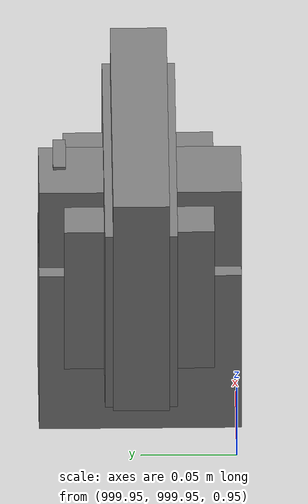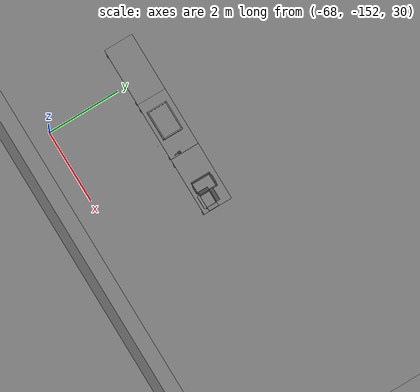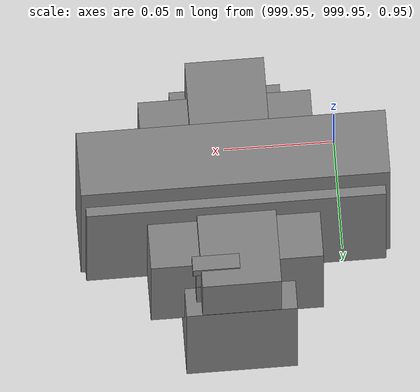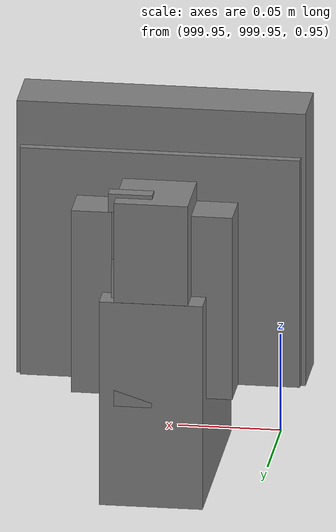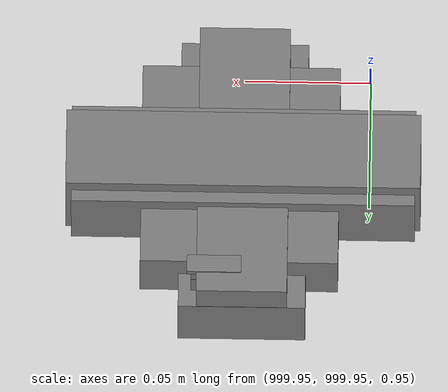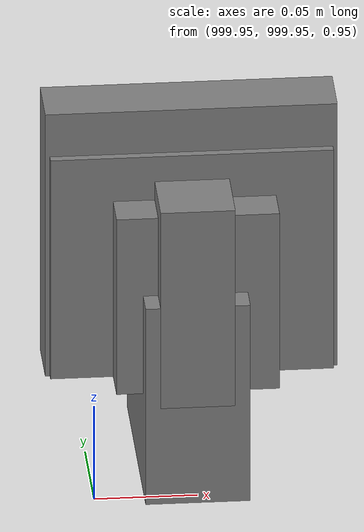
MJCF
<mujoco>
    <option gravity="0.000000000 0.000000000 -9.810000420" timestep="0.0049999999" integrator="implicitfast" density="1.225" viscosity="1.8000001e-05" noslip_iterations="10" iterations="100" sdf_iterations="50">
        <flag multiccd="disable"/>
    </option>
    <size memory="1000M"/>
    <compiler coordinate="local"/>
    <worldbody>
        <light cutoff="30" pos="0 1 1" dir="0 -1 -2"/>
        <light cutoff="30" pos="0 -1 1" dir="0 1 -2"/>
        <body pos="-64.866622925 -149.383972168 30.183746338" euler="89.999984741 89.999946594 0.000000000" name="openloong_gripper_2f85_fix_base_usda_bluebox_01">
            <geom contype="1" conaffinity="1" density="1000" type="box" material="" rgba="0.500000000 0.500000000 0.500000000 1.000000000" solimp="0.899999976 0.949999988 0.001000000" friction="1.000000000 0.005000000 0.000100000" solref="0.020000000 1.000000000" margin="0" condim="3" group="0" pos="0.276580811 0.187225342 0.000068665" quat="0.707106948 0.000077471 0.707106352 0.000077486" size="0.100000001 0.057999998 0.010000000" name="openloong_gripper_2f85_fix_base_usda_geom_F447B181_528C_4D7D_A372_B38C3869CC7E"/>
            <geom contype="1" conaffinity="1" density="1000" type="box" material="" rgba="0.500000000 0.500000000 0.500000000 1.000000000" solimp="0.899999976 0.949999988 0.001000000" friction="1.000000000 0.005000000 0.000100000" solref="0.020000000 1.000000000" margin="0" condim="3" group="0" pos="0.000000000 0.002883911 0.000000000" quat="0.999999881 0.000000000 0.000000000 0.000000000" size="0.254000008 0.003000000 0.172000006" name="openloong_gripper_2f85_fix_base_usda_geom_2CC318BA_EE18_4985_BADE_39C0C8E0BC6A"/>
            <geom contype="1" conaffinity="1" density="1000" type="box" material="" rgba="0.500000000 0.500000000 0.500000000 1.000000000" solimp="0.899999976 0.949999988 0.001000000" friction="1.000000000 0.005000000 0.000100000" solref="0.020000000 1.000000000" margin="0" condim="3" group="0" pos="0.000000000 0.124874115 0.173484802" quat="0.999796331 0.020176515 -0.000000015 0.000000030" size="0.259999990 0.119999997 0.007000000" name="openloong_gripper_2f85_fix_base_usda_geom_E162CEF6_B273_4974_A3B0_552BE1B40F0E"/>
            <geom contype="1" conaffinity="1" density="1000" type="box" material="" rgba="0.500000000 0.500000000 0.500000000 1.000000000" solimp="0.899999976 0.949999988 0.001000000" friction="1.000000000 0.005000000 0.000100000" solref="0.020000000 1.000000000" margin="0" condim="3" group="0" pos="0.000000000 0.124874115 -0.173469543" quat="0.999796331 -0.020176545 -0.000000015 0.000000000" size="0.259999990 0.119999997 0.007000000" name="openloong_gripper_2f85_fix_base_usda_geom_C63A7FC5_A34C_4779_8CFE_5EF5CE1E7A4C"/>
            <geom contype="1" conaffinity="1" density="1000" type="box" material="" rgba="0.500000000 0.500000000 0.500000000 1.000000000" solimp="0.899999976 0.949999988 0.001000000" friction="1.000000000 0.005000000 0.000100000" solref="0.020000000 1.000000000" margin="0" condim="3" group="0" pos="0.000000000 0.214008331 0.188980103" quat="0.999912977 0.013176724 0.000000015 0.000000000" size="0.259999990 0.029999999 0.012500000" name="openloong_gripper_2f85_fix_base_usda_geom_FFEF4732_3557_40A2_8876_5FDF28139C68"/>
            <geom contype="1" conaffinity="1" density="1000" type="box" material="" rgba="0.500000000 0.500000000 0.500000000 1.000000000" solimp="0.899999976 0.949999988 0.001000000" friction="1.000000000 0.005000000 0.000100000" solref="0.020000000 1.000000000" margin="0" condim="3" group="0" pos="-0.258361816 0.125289917 0.001876831" quat="0.702796936 -0.020792112 0.710783124 0.020769298" size="0.189999998 0.119999997 0.009000000" name="openloong_gripper_2f85_fix_base_usda_geom_000D002F_5BA9_4071_A018_3B5C9AB64A25"/>
            <geom contype="1" conaffinity="1" density="1000" type="box" material="" rgba="0.500000000 0.500000000 0.500000000 1.000000000" solimp="0.899999976 0.949999988 0.001000000" friction="1.000000000 0.005000000 0.000100000" solref="0.020000000 1.000000000" margin="0" condim="3" group="0" pos="0.000000000 0.214008331 -0.188980103" quat="0.999912977 -0.013176769 0.000000030 0.000000015" size="0.259999990 0.029999999 0.012500000" name="openloong_gripper_2f85_fix_base_usda_geom_4F3FFFE5_C706_40C6_9B41_E26F4D26D10F"/>
            <geom contype="1" conaffinity="1" density="1000" type="box" material="" rgba="0.500000000 0.500000000 0.500000000 1.000000000" solimp="0.899999976 0.949999988 0.001000000" friction="1.000000000 0.005000000 0.000100000" solref="0.020000000 1.000000000" margin="0" condim="3" group="0" pos="-0.276611328 0.187225342 0.000068665" quat="0.707106650 0.000077441 0.707106709 0.000077456" size="0.100000001 0.057999998 0.010000000" name="openloong_gripper_2f85_fix_base_usda_geom_A7E0A429_A9B7_435C_AF52_6DD4C3660643"/>
            <geom contype="1" conaffinity="1" density="1000" type="box" material="" rgba="0.500000000 0.500000000 0.500000000 1.000000000" solimp="0.899999976 0.949999988 0.001000000" friction="1.000000000 0.005000000 0.000100000" solref="0.020000000 1.000000000" margin="0" condim="3" group="0" pos="0.258331299 0.125289917 0.001876831" quat="0.702851415 0.018856421 0.710823774 -0.019329369" size="0.189999998 0.119999997 0.009000000" name="openloong_gripper_2f85_fix_base_usda_geom_AA3D1C8A_F73A_4281_AA34_B4827791204D"/>
            <freejoint name="openloong_gripper_2f85_fix_base_usda_bluebox_01_joint"/>
            <site size="0.005000000 0.005000000 0.005000000" rgba="0.500000000 0.500000000 0.500000000 1.000000000" pos="0.000000000 0.000000000 0.000000000" quat="0.999961913 0.008726534 0.000000000 0.000000000" group="0" type="sphere" name="openloong_gripper_2f85_fix_base_usda_bluebox_01site"/>
        </body>
        <body pos="-64.496299744 -149.491867065 30.235729218" euler="0.000000000 0.000000000 89.999946594" name="openloong_gripper_2f85_fix_base_usda_cardboardbox_01">
            <geom contype="1" conaffinity="1" density="1000" type="box" material="" rgba="0.500000000 0.500000000 0.500000000 1.000000000" solimp="0.899999976 0.949999988 0.001000000" friction="1.000000000 0.005000000 0.000100000" solref="0.020000000 1.000000000" margin="0" condim="3" group="0" pos="-0.003166199 -0.004086494 0.005052090" quat="1.000000000 0.000000000 0.000000000 0.000000000" size="0.142499998 0.177500010 0.005000000" name="openloong_gripper_2f85_fix_base_usda_geom_43CE8327_6D29_41BC_B522_E796ED36A808"/>
            <geom contype="1" conaffinity="1" density="1000" type="box" material="" rgba="0.500000000 0.500000000 0.500000000 1.000000000" solimp="0.899999976 0.949999988 0.001000000" friction="1.000000000 0.005000000 0.000100000" solref="0.020000000 1.000000000" margin="0" condim="3" group="0" pos="-0.003166199 0.170316696 0.150570869" quat="1.000000000 0.000000000 0.000000000 0.000000000" size="0.142499998 0.005000000 0.149999991" name="openloong_gripper_2f85_fix_base_usda_geom_CFBDE519_CD89_4AE9_91F6_3B461C3485B4"/>
            <geom contype="1" conaffinity="1" density="1000" type="box" material="" rgba="0.500000000 0.500000000 0.500000000 1.000000000" solimp="0.899999976 0.949999988 0.001000000" friction="1.000000000 0.005000000 0.000100000" solref="0.020000000 1.000000000" margin="0" condim="3" group="0" pos="-0.147399902 -0.005307198 0.150570869" quat="1.000000000 0.000000000 0.000000000 0.000000000" size="0.005000000 0.177500010 0.149999991" name="openloong_gripper_2f85_fix_base_usda_geom_E5007F61_0BEE_4027_B8CB_2333C88979A1"/>
            <geom contype="1" conaffinity="1" density="1000" type="box" material="" rgba="0.500000000 0.500000000 0.500000000 1.000000000" solimp="0.899999976 0.949999988 0.001000000" friction="1.000000000 0.005000000 0.000100000" solref="0.020000000 1.000000000" margin="0" condim="3" group="0" pos="0.140275955 -0.005307198 0.150570869" quat="1.000000000 0.000000000 0.000000000 0.000000000" size="0.005000000 0.177500010 0.149999991" name="openloong_gripper_2f85_fix_base_usda_geom_E3D7D577_DE41_4F15_8303_C7E5F9AA2D19"/>
            <geom contype="1" conaffinity="1" density="1000" type="box" material="" rgba="0.500000000 0.500000000 0.500000000 1.000000000" solimp="0.899999976 0.949999988 0.001000000" friction="1.000000000 0.005000000 0.000100000" solref="0.020000000 1.000000000" margin="0" condim="3" group="0" pos="-0.003166199 -0.181550980 0.150570869" quat="1.000000000 0.000000000 0.000000000 0.000000000" size="0.142499998 0.005000000 0.149999991" name="openloong_gripper_2f85_fix_base_usda_geom_040BC586_762C_4F4C_B8F2_EE08219AE228"/>
            <freejoint name="openloong_gripper_2f85_fix_base_usda_cardboardbox_01_joint"/>
            <site size="0.005000000 0.005000000 0.005000000" rgba="0.500000000 0.500000000 0.500000000 1.000000000" pos="0.000000000 0.000000000 0.000000000" quat="0.999961913 0.008726535 0.000000000 0.000000000" group="0" type="sphere" name="openloong_gripper_2f85_fix_base_usda_site_06345618_8A4C_4732_AF45_0E8E8684A4A6"/>
            <body pos="0.139160156 -0.004048347 0.301930904" euler="-179.999954224 49.383502960 179.999954224" name="openloong_gripper_2f85_fix_base_usda_A1_006">
                <geom contype="1" conaffinity="1" density="1000" type="box" material="" rgba="0.500000000 0.500000000 0.500000000 1.000000000" solimp="0.899999976 0.949999988 0.001000000" friction="1.000000000 0.005000000 0.000100000" solref="0.020000000 1.000000000" margin="0" condim="3" group="0" pos="-0.071587563 0.000009537 0.001745224" quat="0.999999881 0.000000000 0.000000000 0.000000000" size="0.071249999 0.179999992 0.002500000" name="openloong_gripper_2f85_fix_base_usda_geom_CFBC5708_8F30_4DDA_A62C_83BFA14B9CB3"/>
                <joint armature="0" stiffness="0.07" damping="0.0099999998" axis="0.000000 1.000000 0.000000" type="hinge" name="openloong_gripper_2f85_fix_base_usda_A1_006"/>
            </body>
            <body pos="-0.145902634 -0.004086494 0.301938057" euler="-180.000000000 -60.000011444 -180.000000000" name="openloong_gripper_2f85_fix_base_usda_A2_006">
                <geom contype="1" conaffinity="1" density="1000" type="box" material="" rgba="0.500000000 0.500000000 0.500000000 1.000000000" solimp="0.899999976 0.949999988 0.001000000" friction="1.000000000 0.005000000 0.000100000" solref="0.020000000 1.000000000" margin="0" condim="3" group="0" pos="0.071268082 0.000009537 0.002717972" quat="0.000002921 0.000000000 -0.000000030 0.999999881" size="0.071249999 0.179999992 0.002500000" name="openloong_gripper_2f85_fix_base_usda_geom_6D7EE55A_9054_4E93_A3EE_42F26806022C"/>
                <joint armature="0" stiffness="0.07" damping="0.0099999998" axis="0.000000 1.000000 0.000000" type="hinge" name="openloong_gripper_2f85_fix_base_usda_A2_006"/>
            </body>
            <body pos="-0.003385544 0.175991058 0.301930904" euler="-125.858116150 -0.000004561 0.000002331" name="openloong_gripper_2f85_fix_base_usda_B2_006">
                <geom contype="1" conaffinity="1" density="1000" type="box" material="" rgba="0.500000000 0.500000000 0.500000000 1.000000000" solimp="0.899999976 0.949999988 0.001000000" friction="1.000000000 0.005000000 0.000100000" solref="0.020000000 1.000000000" margin="0" condim="3" group="0" pos="0.000009537 -0.070939064 -0.002470016" quat="0.999614120 0.027776197 -0.000000015 0.000000030" size="0.137500003 0.064999998 0.005000000" name="openloong_gripper_2f85_fix_base_usda_geom_674A2C06_734F_4A89_BC5D_0BB2CD66F64E"/>
                <joint armature="0" stiffness="0.07" damping="0.0099999998" axis="1.000000 0.000000 0.000000" type="hinge" name="openloong_gripper_2f85_fix_base_usda_B2_006"/>
            </body>
            <body pos="-0.003385544 -0.184140205 0.301938057" euler="147.805557251 0.000000000 0.000000000" name="openloong_gripper_2f85_fix_base_usda_B1_006">
                <geom contype="1" conaffinity="1" density="1000" type="box" material="" rgba="0.500000000 0.500000000 0.500000000 1.000000000" solimp="0.899999976 0.949999988 0.001000000" friction="1.000000000 0.005000000 0.000100000" solref="0.020000000 1.000000000" margin="0" condim="3" group="0" pos="-0.000028610 0.070202351 -0.002703667" quat="0.999614179 -0.027776167 0.000000000 0.000000000" size="0.137500003 0.064999998 0.005000000" name="openloong_gripper_2f85_fix_base_usda_geom_ED59E1EF_F814_466E_B1DE_D2BF3AEB87CD"/>
                <joint armature="0" stiffness="0.07" damping="0.0099999998" axis="1.000000 0.000000 0.000000" type="hinge" name="openloong_gripper_2f85_fix_base_usda_B1_006"/>
            </body>
        </body>
        <body pos="-65.882858276 -149.481979370 30.229999542" euler="-64.487716675 0.000000000 0.000000000" name="openloong_gripper_2f85_fix_base_usda_Barcode">
            <geom contype="1" conaffinity="1" density="1000" type="box" material="" rgba="0.500000000 0.500000000 0.500000000 1.000000000" solimp="0.899999976 0.949999988 0.001000000" friction="1.000000000 0.005000000 0.000100000" solref="0.020000000 1.000000000" margin="0" condim="3" group="0" pos="0.000000000 0.013038635 0.001419067" quat="0.000000000 0.000000000 0.000000000 1.000000119" size="0.034000002 0.010000000 0.017999999" name="openloong_gripper_2f85_fix_base_usda_geom_12978741_434A_4DC9_AEA9_05A2F3733F47"/>
            <geom contype="1" conaffinity="1" density="1000" type="box" material="" rgba="0.500000000 0.500000000 0.500000000 1.000000000" solimp="0.899999976 0.949999988 0.001000000" friction="1.000000000 0.005000000 0.000100000" solref="0.020000000 1.000000000" margin="0" condim="3" group="0" pos="0.000000000 -0.035301208 -0.007095337" quat="0.000000000 0.000000000 -0.043619365 0.999048233" size="0.028999999 0.010000000 0.020000000" name="openloong_gripper_2f85_fix_base_usda_geom_34260EBD_749D_4735_85B9_055111AE03B6"/>
            <geom contype="1" conaffinity="1" density="1000" type="box" material="" rgba="0.500000000 0.500000000 0.500000000 1.000000000" solimp="0.899999976 0.949999988 0.001000000" friction="1.000000000 0.005000000 0.000100000" solref="0.020000000 1.000000000" margin="0" condim="3" group="0" pos="0.000000000 -0.043411255 -0.011749268" quat="0.922262907 0.386563420 0.000000000 0.000000000" size="0.026000001 0.010000000 0.020000000" name="openloong_gripper_2f85_fix_base_usda_geom_1667A818_6C29_4105_895C_627913E19EF8"/>
            <geom contype="1" conaffinity="1" density="1000" type="box" material="" rgba="0.500000000 0.500000000 0.500000000 1.000000000" solimp="0.899999976 0.949999988 0.001000000" friction="1.000000000 0.005000000 0.000100000" solref="0.020000000 1.000000000" margin="0" condim="3" group="0" pos="0.000000000 -0.016967773 -0.031860352" quat="0.000000000 0.000000000 0.000000000 1.000000119" size="0.008000000 0.010000000 0.013000000" name="openloong_gripper_2f85_fix_base_usda_geom_B9949253_2FA7_4574_9A7E_C52BF55FB018"/>
            <geom contype="1" conaffinity="1" density="1000" type="box" material="" rgba="0.500000000 0.500000000 0.500000000 1.000000000" solimp="0.899999976 0.949999988 0.001000000" friction="1.000000000 0.005000000 0.000100000" solref="0.020000000 1.000000000" margin="0" condim="3" group="0" pos="0.000000000 -0.001869202 0.000312805" quat="0.953716993 0.300705761 0.000000000 0.000000000" size="0.032000002 0.010000000 0.018999999" name="openloong_gripper_2f85_fix_base_usda_geom_C7B2BE1E_1F02_4490_9D12_08ABF662505B"/>
            <geom contype="1" conaffinity="1" density="1000" type="box" material="" rgba="0.500000000 0.500000000 0.500000000 1.000000000" solimp="0.899999976 0.949999988 0.001000000" friction="1.000000000 0.005000000 0.000100000" solref="0.020000000 1.000000000" margin="0" condim="3" group="0" pos="0.000000000 -0.019531250 -0.003173828" quat="0.953716993 0.300705761 0.000000000 0.000000000" size="0.030999999 0.010000000 0.020000000" name="openloong_gripper_2f85_fix_base_usda_geom_F9D9BE66_81EF_4B6D_AFFB_8677EA73D4F7"/>
            <geom contype="1" conaffinity="1" density="1000" type="box" material="" rgba="0.500000000 0.500000000 0.500000000 1.000000000" solimp="0.899999976 0.949999988 0.001000000" friction="1.000000000 0.005000000 0.000100000" solref="0.020000000 1.000000000" margin="0" condim="3" group="0" pos="0.000000000 -0.035301208 -0.007095337" quat="0.953716993 0.300705761 0.000000000 0.000000000" size="0.028999999 0.010000000 0.020000000" name="openloong_gripper_2f85_fix_base_usda_geom_A860EF3B_B3CD_4070_BE65_DDA5A7E2D832"/>
            <geom contype="1" conaffinity="1" density="1000" type="box" material="" rgba="0.500000000 0.500000000 0.500000000 1.000000000" solimp="0.899999976 0.949999988 0.001000000" friction="1.000000000 0.005000000 0.000100000" solref="0.020000000 1.000000000" margin="0" condim="3" group="0" pos="0.000000000 -0.042617798 -0.071121216" quat="0.000000000 0.000000000 0.000000000 1.000000119" size="0.013000000 0.021000000 0.059999999" name="openloong_gripper_2f85_fix_base_usda_geom_4B44F1C1_4449_4CE8_A217_043E443C70E2"/>
            <freejoint name="openloong_gripper_2f85_fix_base_usda_Barcode_joint"/>
            <site size="0.005000000 0.005000000 0.005000000" rgba="0.500000000 0.500000000 0.500000000 1.000000000" pos="0.000000000 0.000000000 0.000000000" quat="1.000000000 0.000000000 0.000000000 0.000000000" group="0" type="sphere" name="openloong_gripper_2f85_fix_base_usda_Barcode_site"/>
        </body>
        <body pos="-66.745018005 -149.392349243 30.184000015" euler="0.000000000 0.000000000 89.999946594" name="[22331550337168]_Basket_01">
            <geom contype="1" conaffinity="1" density="1000" type="box" material="" rgba="0.500000000 0.500000000 0.500000000 1.000000000" solimp="0.899999976 0.949999988 0.001000000" friction="1.000000000 0.005000000 0.000100000" solref="0.020000000 1.000000000" margin="0" condim="3" group="0" pos="-0.052425385 0.389207840 0.089787483" quat="0.707107008 0.000000000 0.000000000 0.707106411" size="0.014249999 0.014249999 0.059999999" name="[22331550337168]_geom_607681CC_9B6E_42CD_ADC8_7921E3E490BB"/>
            <geom contype="1" conaffinity="1" density="1000" type="box" material="" rgba="0.500000000 0.500000000 0.500000000 1.000000000" solimp="0.899999976 0.949999988 0.001000000" friction="1.000000000 0.005000000 0.000100000" solref="0.020000000 1.000000000" margin="0" condim="3" group="0" pos="0.264015198 -0.133043289 0.089787483" quat="0.707107008 0.000000000 0.000000000 0.707106411" size="0.014249999 0.014249999 0.059999999" name="[22331550337168]_geom_6D3F1DA6_B8CA_4D7C_8138_622BD700F44B"/>
            <geom contype="1" conaffinity="1" density="1000" type="box" material="" rgba="0.500000000 0.500000000 0.500000000 1.000000000" solimp="0.899999976 0.949999988 0.001000000" friction="1.000000000 0.005000000 0.000100000" solref="0.020000000 1.000000000" margin="0" condim="3" group="0" pos="-0.264015198 -0.265548706 0.089793205" quat="0.707107008 0.000000000 0.000000000 0.707106411" size="0.014249999 0.014249999 0.059999999" name="[22331550337168]_geom_39438EF5_AF28_47B8_9D30_406E4433A8B7"/>
            <geom contype="1" conaffinity="1" density="1000" type="box" material="" rgba="0.500000000 0.500000000 0.500000000 1.000000000" solimp="0.899999976 0.949999988 0.001000000" friction="1.000000000 0.005000000 0.000100000" solref="0.020000000 1.000000000" margin="0" condim="3" group="0" pos="-0.160263062 -0.389322281 0.089793205" quat="0.707107008 0.000000000 0.000000000 0.707106411" size="0.014249999 0.014249999 0.059999999" name="[22331550337168]_geom_AE63E9A8_36C5_4696_9900_D69AC1807CAC"/>
            <geom contype="1" conaffinity="1" density="1000" type="box" material="" rgba="0.500000000 0.500000000 0.500000000 1.000000000" solimp="0.899999976 0.949999988 0.001000000" friction="1.000000000 0.005000000 0.000100000" solref="0.020000000 1.000000000" margin="0" condim="3" group="0" pos="0.162265778 -0.389322281 0.089787483" quat="0.707107008 0.000000000 0.000000000 0.707106411" size="0.014249999 0.014249999 0.059999999" name="[22331550337168]_geom_7F756DFB_06D1_46B9_B1DD_84E9A42C983B"/>
            <geom contype="1" conaffinity="1" density="1000" type="box" material="" rgba="0.500000000 0.500000000 0.500000000 1.000000000" solimp="0.899999976 0.949999988 0.001000000" friction="1.000000000 0.005000000 0.000100000" solref="0.020000000 1.000000000" margin="0" condim="3" group="0" pos="0.264015198 0.389207840 0.089787483" quat="0.707107008 0.000000000 0.000000000 0.707106411" size="0.014249999 0.014249999 0.059999999" name="[22331550337168]_geom_7F01861E_348E_4D07_AFE6_9F90F3F35200"/>
            <geom contype="1" conaffinity="1" density="1000" type="box" material="" rgba="0.500000000 0.500000000 0.500000000 1.000000000" solimp="0.899999976 0.949999988 0.001000000" friction="1.000000000 0.005000000 0.000100000" solref="0.020000000 1.000000000" margin="0" condim="3" group="0" pos="-0.264015198 -0.133043289 0.089793205" quat="0.707107008 0.000000000 0.000000000 0.707106411" size="0.014249999 0.014249999 0.059999999" name="[22331550337168]_geom_9D3EEF12_A193_49B8_8391_142810B51196"/>
            <geom contype="1" conaffinity="1" density="1000" type="box" material="" rgba="0.500000000 0.500000000 0.500000000 1.000000000" solimp="0.899999976 0.949999988 0.001000000" friction="1.000000000 0.005000000 0.000100000" solref="0.020000000 1.000000000" margin="0" condim="3" group="0" pos="-0.264026642 0.269256592 0.089793205" quat="0.707107008 0.000000000 0.000000000 0.707106411" size="0.014249999 0.014249999 0.059999999" name="[22331550337168]_geom_FD320542_4A7F_479B_9F47_B76F253BF1C5"/>
            <geom contype="1" conaffinity="1" density="1000" type="box" material="" rgba="0.500000000 0.500000000 0.500000000 1.000000000" solimp="0.899999976 0.949999988 0.001000000" friction="1.000000000 0.005000000 0.000100000" solref="0.020000000 1.000000000" margin="0" condim="3" group="0" pos="0.054462433 0.389207840 0.089787483" quat="0.707107008 0.000000000 0.000000000 0.707106411" size="0.014249999 0.014249999 0.059999999" name="[22331550337168]_geom_1A9EC8A6_D7F8_4E49_919D_4DA4193759DD"/>
            <geom contype="1" conaffinity="1" density="1000" type="box" material="" rgba="0.500000000 0.500000000 0.500000000 1.000000000" solimp="0.899999976 0.949999988 0.001000000" friction="1.000000000 0.005000000 0.000100000" solref="0.020000000 1.000000000" margin="0" condim="3" group="0" pos="0.054462433 -0.389322281 0.089787483" quat="0.707107008 0.000000000 0.000000000 0.707106411" size="0.014249999 0.014249999 0.059999999" name="[22331550337168]_geom_8ECF3489_2866_4864_87C7_08674708A985"/>
            <geom contype="1" conaffinity="1" density="1000" type="box" material="" rgba="0.500000000 0.500000000 0.500000000 1.000000000" solimp="0.899999976 0.949999988 0.001000000" friction="1.000000000 0.005000000 0.000100000" solref="0.020000000 1.000000000" margin="0" condim="3" group="0" pos="0.264015198 0.269256592 0.089793205" quat="0.707107008 0.000000000 0.000000000 0.707106411" size="0.014249999 0.014249999 0.059999999" name="[22331550337168]_geom_31AD0763_8BE6_433B_8178_A9D9E81A366B"/>
            <geom contype="1" conaffinity="1" density="1000" type="box" material="" rgba="0.500000000 0.500000000 0.500000000 1.000000000" solimp="0.899999976 0.949999988 0.001000000" friction="1.000000000 0.005000000 0.000100000" solref="0.020000000 1.000000000" margin="0" condim="3" group="0" pos="0.264015198 -0.389322281 0.089787483" quat="0.707107008 0.000000000 0.000000000 0.707106411" size="0.014249999 0.014249999 0.059999999" name="[22331550337168]_geom_B56E9575_F737_4BF3_AB5A_13DD7552B734"/>
            <geom contype="1" conaffinity="1" density="1000" type="box" material="" rgba="0.500000000 0.500000000 0.500000000 1.000000000" solimp="0.899999976 0.949999988 0.001000000" friction="1.000000000 0.005000000 0.000100000" solref="0.020000000 1.000000000" margin="0" condim="3" group="0" pos="0.000000000 0.000000000 0.015998840" quat="0.707107008 0.000000000 0.000000000 0.707106411" size="0.403499991 0.279000014 0.015750000" name="[22331550337168]_geom_BF3B699F_C969_4352_94F5_8C497B4F7FA8"/>
            <geom contype="1" conaffinity="1" density="1000" type="box" material="" rgba="0.500000000 0.500000000 0.500000000 1.000000000" solimp="0.899999976 0.949999988 0.001000000" friction="1.000000000 0.005000000 0.000100000" solref="0.020000000 1.000000000" margin="0" condim="3" group="0" pos="0.000000000 -0.389476776 0.163619041" quat="0.707107008 0.000000000 0.000000000 0.707106411" size="0.015000000 0.277500004 0.015750000" name="[22331550337168]_geom_B6B18CFA_5D60_4722_B067_799E2388E8D0"/>
            <geom contype="1" conaffinity="1" density="1000" type="box" material="" rgba="0.500000000 0.500000000 0.500000000 1.000000000" solimp="0.899999976 0.949999988 0.001000000" friction="1.000000000 0.005000000 0.000100000" solref="0.020000000 1.000000000" margin="0" condim="3" group="0" pos="0.162265778 0.389207840 0.089787483" quat="0.707107008 0.000000000 0.000000000 0.707106411" size="0.014249999 0.014249999 0.059999999" name="[22331550337168]_geom_CC1D0C16_9D7B_4B5E_8795_A4283A60E71A"/>
            <geom contype="1" conaffinity="1" density="1000" type="box" material="" rgba="0.500000000 0.500000000 0.500000000 1.000000000" solimp="0.899999976 0.949999988 0.001000000" friction="1.000000000 0.005000000 0.000100000" solref="0.020000000 1.000000000" margin="0" condim="3" group="0" pos="0.000000000 0.389471054 0.163619041" quat="0.707107008 0.000000000 0.000000000 0.707106411" size="0.015000000 0.277500004 0.015750000" name="[22331550337168]_geom_212689DB_6568_4A16_BD35_6ABEDC34ECB9"/>
            <geom contype="1" conaffinity="1" density="1000" type="box" material="" rgba="0.500000000 0.500000000 0.500000000 1.000000000" solimp="0.899999976 0.949999988 0.001000000" friction="1.000000000 0.005000000 0.000100000" solref="0.020000000 1.000000000" margin="0" condim="3" group="0" pos="-0.263511658 0.000000000 0.163619041" quat="0.707107008 0.000000000 0.000000000 0.707106411" size="0.403499991 0.015000000 0.015750000" name="[22331550337168]_geom_E6E66ECE_4190_44C0_BC9D_40FCFF30CDC0"/>
            <geom contype="1" conaffinity="1" density="1000" type="box" material="" rgba="0.500000000 0.500000000 0.500000000 1.000000000" solimp="0.899999976 0.949999988 0.001000000" friction="1.000000000 0.005000000 0.000100000" solref="0.020000000 1.000000000" margin="0" condim="3" group="0" pos="-0.264015198 0.141334534 0.089793205" quat="0.707107008 0.000000000 0.000000000 0.707106411" size="0.014249999 0.014249999 0.059999999" name="[22331550337168]_geom_ABBCE5C7_412C_4CF5_9AF7_C62A9EE464D6"/>
            <geom contype="1" conaffinity="1" density="1000" type="box" material="" rgba="0.500000000 0.500000000 0.500000000 1.000000000" solimp="0.899999976 0.949999988 0.001000000" friction="1.000000000 0.005000000 0.000100000" solref="0.020000000 1.000000000" margin="0" condim="3" group="0" pos="0.264015198 -0.265548706 0.089787483" quat="0.707107008 0.000000000 0.000000000 0.707106411" size="0.014249999 0.014249999 0.059999999" name="[22331550337168]_geom_6422D408_7E05_462C_BDBA_13DD5D4281C8"/>
            <geom contype="1" conaffinity="1" density="1000" type="box" material="" rgba="0.500000000 0.500000000 0.500000000 1.000000000" solimp="0.899999976 0.949999988 0.001000000" friction="1.000000000 0.005000000 0.000100000" solref="0.020000000 1.000000000" margin="0" condim="3" group="0" pos="-0.160263062 0.389207840 0.089787483" quat="0.707107008 0.000000000 0.000000000 0.707106411" size="0.014249999 0.014249999 0.059999999" name="[22331550337168]_geom_E106CF4F_C8AB_4E41_BAF3_3D7641423A18"/>
            <geom contype="1" conaffinity="1" density="1000" type="box" material="" rgba="0.500000000 0.500000000 0.500000000 1.000000000" solimp="0.899999976 0.949999988 0.001000000" friction="1.000000000 0.005000000 0.000100000" solref="0.020000000 1.000000000" margin="0" condim="3" group="0" pos="-0.052425385 -0.389322281 0.089787483" quat="0.707107008 0.000000000 0.000000000 0.707106411" size="0.014249999 0.014249999 0.059999999" name="[22331550337168]_geom_319A4A25_EDC2_45E1_803F_EA48C9DF326C"/>
            <geom contype="1" conaffinity="1" density="1000" type="box" material="" rgba="0.500000000 0.500000000 0.500000000 1.000000000" solimp="0.899999976 0.949999988 0.001000000" friction="1.000000000 0.005000000 0.000100000" solref="0.020000000 1.000000000" margin="0" condim="3" group="0" pos="-0.264026642 -0.389322281 0.089793205" quat="0.707107008 0.000000000 0.000000000 0.707106411" size="0.014249999 0.014249999 0.059999999" name="[22331550337168]_geom_7C4E14C7_774D_4F8E_9D4A_40D20AA50058"/>
            <geom contype="1" conaffinity="1" density="1000" type="box" material="" rgba="0.500000000 0.500000000 0.500000000 1.000000000" solimp="0.899999976 0.949999988 0.001000000" friction="1.000000000 0.005000000 0.000100000" solref="0.020000000 1.000000000" margin="0" condim="3" group="0" pos="0.264015198 0.141334534 0.089787483" quat="0.707107008 0.000000000 0.000000000 0.707106411" size="0.014249999 0.014249999 0.059999999" name="[22331550337168]_geom_4A756519_732E_4015_9D95_BFCBDD70DC13"/>
            <geom contype="1" conaffinity="1" density="1000" type="box" material="" rgba="0.500000000 0.500000000 0.500000000 1.000000000" solimp="0.899999976 0.949999988 0.001000000" friction="1.000000000 0.005000000 0.000100000" solref="0.020000000 1.000000000" margin="0" condim="3" group="0" pos="-0.264015198 0.389207840 0.089793205" quat="0.707107008 0.000000000 0.000000000 0.707106411" size="0.014249999 0.014249999 0.059999999" name="[22331550337168]_geom_64EA3CE8_6089_4FEA_A51B_C32DC6A3FA25"/>
            <geom contype="1" conaffinity="1" density="1000" type="box" material="" rgba="0.500000000 0.500000000 0.500000000 1.000000000" solimp="0.899999976 0.949999988 0.001000000" friction="1.000000000 0.005000000 0.000100000" solref="0.020000000 1.000000000" margin="0" condim="3" group="0" pos="0.264015198 0.004480362 0.089787483" quat="0.707107008 0.000000000 0.000000000 0.707106411" size="0.014249999 0.014249999 0.059999999" name="[22331550337168]_geom_B5E07887_5F2A_4BAE_8D6F_87A727235E71"/>
            <geom contype="1" conaffinity="1" density="1000" type="box" material="" rgba="0.500000000 0.500000000 0.500000000 1.000000000" solimp="0.899999976 0.949999988 0.001000000" friction="1.000000000 0.005000000 0.000100000" solref="0.020000000 1.000000000" margin="0" condim="3" group="0" pos="0.263694763 -0.000011444 0.163619041" quat="0.707107008 0.000000000 0.000000000 0.707106411" size="0.403499991 0.015000000 0.015750000" name="[22331550337168]_geom_A655D087_7538_427D_B801_F8C123DBA780"/>
            <geom contype="1" conaffinity="1" density="1000" type="box" material="" rgba="0.500000000 0.500000000 0.500000000 1.000000000" solimp="0.899999976 0.949999988 0.001000000" friction="1.000000000 0.005000000 0.000100000" solref="0.020000000 1.000000000" margin="0" condim="3" group="0" pos="-0.264015198 0.004480362 0.089793205" quat="0.707107008 0.000000000 0.000000000 0.707106411" size="0.014249999 0.014249999 0.059999999" name="[22331550337168]_geom_829F04BF_AB42_4B3A_B936_60DD7066DE64"/>
            <freejoint name="[22331550337168]_joint_6D791FE7_DAC3_47F8_8796_74DFA5EDEF08"/>
        </body>
        <body pos="0.000000000 0.000000000 0.000000000" euler="0.000000000 0.000000000 0.000000000" name="Static Objects_Static Objects">
            <geom contype="1" conaffinity="1" density="1000" type="box" material="" rgba="0.500000000 0.500000000 0.500000000 1.000000000" solimp="0.899999976 0.949999988 0.001000000" friction="1.000000000 0.005000000 0.000100000" solref="0.020000000 1.000000000" margin="0" condim="3" group="0" pos="-67.544113159 -149.365814209 29.727830887" quat="0.500000417 0.499999970 0.499999553 0.499999970" size="0.381000012 0.319999993 0.041000001" name="Static Objects_geom_24768EDD_09C7_4540_85D3_406438908FBD"/>
            <geom contype="1" conaffinity="1" density="1000" type="box" material="" rgba="0.500000000 0.500000000 0.500000000 1.000000000" solimp="0.899999976 0.949999988 0.001000000" friction="1.000000000 0.005000000 0.000100000" solref="0.020000000 1.000000000" margin="0" condim="3" group="0" pos="-68.239501953 -149.365814209 30.086868286" quat="0.500000417 0.499999970 0.499999553 0.499999970" size="0.370999992 0.039500002 0.745000005" name="Static Objects_geom_4DC453F8_B74B_420B_9BEF_99CD1E17477A"/>
            <geom contype="1" conaffinity="1" density="1000" type="box" material="" rgba="0.500000000 0.500000000 0.500000000 1.000000000" solimp="0.899999976 0.949999988 0.001000000" friction="1.000000000 0.005000000 0.000100000" solref="0.020000000 1.000000000" margin="0" condim="3" group="0" pos="-68.239501953 -149.365814209 30.147235870" quat="0.500000417 0.499999970 0.499999553 0.499999970" size="0.400000006 0.022000000 0.800000012" name="Static Objects_geom_D1BA9A0A_5BFF_4EF5_AAE5_1B9BE9A78F3F"/>
            <geom contype="1" conaffinity="1" density="1000" type="box" material="" rgba="0.500000000 0.500000000 0.500000000 1.000000000" solimp="0.899999976 0.949999988 0.001000000" friction="1.000000000 0.005000000 0.000100000" solref="0.020000000 1.000000000" margin="0" condim="3" group="0" pos="-68.934890747 -149.365814209 29.727830887" quat="0.500000417 0.499999970 0.499999553 0.499999970" size="0.381000012 0.319999993 0.041000001" name="Static Objects_geom_461BE2A7_015F_45F2_AF11_0E7D75AAA8D6"/>
            <geom contype="1" conaffinity="1" density="1000" type="box" material="" rgba="0.500000000 0.500000000 0.500000000 1.000000000" solimp="0.899999976 0.949999988 0.001000000" friction="1.000000000 0.005000000 0.000100000" solref="0.020000000 1.000000000" margin="0" condim="3" group="0" pos="-68.239501953 -149.365814209 29.561563492" quat="0.500000417 0.499999970 0.499999553 0.499999970" size="0.020000000 0.022000000 0.660000026" name="Static Objects_geom_7A371B00_1687_4012_B675_18EC3B45A72F"/>
            <geom contype="1" conaffinity="1" density="1000" type="box" material="" rgba="0.500000000 0.500000000 0.500000000 1.000000000" solimp="0.899999976 0.949999988 0.001000000" friction="1.000000000 0.005000000 0.000100000" solref="0.020000000 1.000000000" margin="0" condim="3" group="0" pos="-65.945671082 -149.365814209 29.727830887" quat="0.500000417 0.499999970 0.499999553 0.499999970" size="0.381000012 0.319999993 0.041000001" name="Static Objects_geom_837A6BD9_DD7A_4AC7_A135_A4609AA04396"/>
            <geom contype="1" conaffinity="1" density="1000" type="box" material="" rgba="0.500000000 0.500000000 0.500000000 1.000000000" solimp="0.899999976 0.949999988 0.001000000" friction="1.000000000 0.005000000 0.000100000" solref="0.020000000 1.000000000" margin="0" condim="3" group="0" pos="-66.641059875 -149.365814209 30.086868286" quat="0.500000417 0.499999970 0.499999553 0.499999970" size="0.370999992 0.039500002 0.745000005" name="Static Objects_geom_C4C7C55D_A532_4A37_917F_C482903DCCCD"/>
            <geom contype="1" conaffinity="1" density="1000" type="box" material="" rgba="0.500000000 0.500000000 0.500000000 1.000000000" solimp="0.899999976 0.949999988 0.001000000" friction="1.000000000 0.005000000 0.000100000" solref="0.020000000 1.000000000" margin="0" condim="3" group="0" pos="-66.641059875 -149.365814209 30.147235870" quat="0.500000417 0.499999970 0.499999553 0.499999970" size="0.400000006 0.022000000 0.800000012" name="Static Objects_geom_FBB153BC_1EBC_47C3_A416_E0816680223F"/>
            <geom contype="1" conaffinity="1" density="1000" type="box" material="" rgba="0.500000000 0.500000000 0.500000000 1.000000000" solimp="0.899999976 0.949999988 0.001000000" friction="1.000000000 0.005000000 0.000100000" solref="0.020000000 1.000000000" margin="0" condim="3" group="0" pos="-67.336448669 -149.365814209 29.727830887" quat="0.500000417 0.499999970 0.499999553 0.499999970" size="0.381000012 0.319999993 0.041000001" name="Static Objects_geom_2C2489EB_AB4B_412C_85FE_C6EFD62AA990"/>
            <geom contype="1" conaffinity="1" density="1000" type="box" material="" rgba="0.500000000 0.500000000 0.500000000 1.000000000" solimp="0.899999976 0.949999988 0.001000000" friction="1.000000000 0.005000000 0.000100000" solref="0.020000000 1.000000000" margin="0" condim="3" group="0" pos="-66.641059875 -149.365814209 29.561563492" quat="0.500000417 0.499999970 0.499999553 0.499999970" size="0.020000000 0.022000000 0.660000026" name="Static Objects_geom_D8C6CA51_BEAB_4BC4_B18D_97E47C1FE8E7"/>
            <geom contype="1" conaffinity="1" density="1000" type="box" material="" rgba="0.500000000 0.500000000 0.500000000 1.000000000" solimp="0.899999976 0.949999988 0.001000000" friction="1.000000000 0.005000000 0.000100000" solref="0.020000000 1.000000000" margin="0" condim="3" group="0" pos="-64.338577271 -149.365814209 29.727830887" quat="0.500000417 0.499999970 0.499999553 0.499999970" size="0.381000012 0.319999993 0.041000001" name="Static Objects_geom_E4B94F38_250F_4EAA_A501_D2AA88FC6438"/>
            <geom contype="1" conaffinity="1" density="1000" type="box" material="" rgba="0.500000000 0.500000000 0.500000000 1.000000000" solimp="0.899999976 0.949999988 0.001000000" friction="1.000000000 0.005000000 0.000100000" solref="0.020000000 1.000000000" margin="0" condim="3" group="0" pos="-65.033966064 -149.365814209 30.086868286" quat="0.500000417 0.499999970 0.499999553 0.499999970" size="0.370999992 0.039500002 0.745000005" name="Static Objects_geom_AA04008F_32A2_464D_A817_7445BBA98F9E"/>
            <geom contype="1" conaffinity="1" density="1000" type="box" material="" rgba="0.500000000 0.500000000 0.500000000 1.000000000" solimp="0.899999976 0.949999988 0.001000000" friction="1.000000000 0.005000000 0.000100000" solref="0.020000000 1.000000000" margin="0" condim="3" group="0" pos="-65.033966064 -149.365814209 30.147235870" quat="0.500000417 0.499999970 0.499999553 0.499999970" size="0.400000006 0.022000000 0.800000012" name="Static Objects_geom_F788C7E4_5108_4CB0_A85F_456CBABA4532"/>
            <geom contype="1" conaffinity="1" density="1000" type="box" material="" rgba="0.500000000 0.500000000 0.500000000 1.000000000" solimp="0.899999976 0.949999988 0.001000000" friction="1.000000000 0.005000000 0.000100000" solref="0.020000000 1.000000000" margin="0" condim="3" group="0" pos="-65.729354858 -149.365814209 29.727830887" quat="0.500000417 0.499999970 0.499999553 0.499999970" size="0.381000012 0.319999993 0.041000001" name="Static Objects_geom_E5E821A4_7484_4861_AE98_9850121EEF2F"/>
            <geom contype="1" conaffinity="1" density="1000" type="box" material="" rgba="0.500000000 0.500000000 0.500000000 1.000000000" solimp="0.899999976 0.949999988 0.001000000" friction="1.000000000 0.005000000 0.000100000" solref="0.020000000 1.000000000" margin="0" condim="3" group="0" pos="-65.033966064 -149.365814209 29.561563492" quat="0.500000417 0.499999970 0.499999553 0.499999970" size="0.020000000 0.022000000 0.660000026" name="Static Objects_geom_4B454E9A_9574_45A3_A9D6_EF0C9F777C93"/>
            <geom contype="1" conaffinity="1" density="1000" type="box" material="" rgba="0.500000000 0.500000000 0.500000000 1.000000000" solimp="0.899999976 0.949999988 0.001000000" friction="1.000000000 0.005000000 0.000100000" solref="0.020000000 1.000000000" margin="0" condim="3" group="0" pos="-61.754566193 -137.853729248 33.906845093" quat="0.707107067 0.000000000 0.000000000 0.707106471" size="0.759999990 0.759999990 4.500000000" name="Static Objects_geom_F3A4F2E8_6861_4A21_B554_EA90AC6CBBB0"/>
            <geom contype="1" conaffinity="1" density="1000" type="box" material="" rgba="0.500000000 0.500000000 0.500000000 1.000000000" solimp="0.899999976 0.949999988 0.001000000" friction="1.000000000 0.005000000 0.000100000" solref="0.020000000 1.000000000" margin="0" condim="3" group="0" pos="-57.511135101 -144.927108765 31.707921982" quat="1.000000000 0.000000000 0.000000000 0.000000000" size="0.200000003 8.000000000 2.299999952" name="Static Objects_geom_46B9422C_9F7A_4383_A8AA_492D9E7AB2BE"/>
            <geom contype="1" conaffinity="1" density="1000" type="box" material="" rgba="0.500000000 0.500000000 0.500000000 1.000000000" solimp="0.899999976 0.949999988 0.001000000" friction="1.000000000 0.005000000 0.000100000" solref="0.020000000 1.000000000" margin="0" condim="3" group="0" pos="-80.517646790 -157.574050903 31.688196182" quat="0.707107067 0.000000000 0.000000000 0.707106471" size="0.600000024 0.600000024 2.299999952" name="Static Objects_geom_A2F8EC55_E2A2_4194_8EA0_F944CBBF2B0B"/>
            <geom contype="1" conaffinity="1" density="1000" type="box" material="" rgba="0.500000000 0.500000000 0.500000000 1.000000000" solimp="0.899999976 0.949999988 0.001000000" friction="1.000000000 0.005000000 0.000100000" solref="0.020000000 1.000000000" margin="0" condim="3" group="0" pos="-80.711044312 -147.414932251 31.666158676" quat="1.000000000 0.000000000 0.000000000 0.000000000" size="0.200000003 10.000000000 2.299999952" name="Static Objects_geom_9191D0C6_853E_4747_9B87_DB9826F3EE3F"/>
            <geom contype="1" conaffinity="1" density="1000" type="box" material="" rgba="0.500000000 0.500000000 0.500000000 1.000000000" solimp="0.899999976 0.949999988 0.001000000" friction="1.000000000 0.005000000 0.000100000" solref="0.020000000 1.000000000" margin="0" condim="3" group="0" pos="-57.687217712 -137.434692383 31.688196182" quat="0.707107067 0.000000000 0.000000000 0.707106471" size="0.600000024 0.600000024 2.299999952" name="Static Objects_geom_25710C6A_08FD_4C34_997E_F167006E8513"/>
            <geom contype="1" conaffinity="1" density="1000" type="box" material="" rgba="0.500000000 0.500000000 0.500000000 1.000000000" solimp="0.899999976 0.949999988 0.001000000" friction="1.000000000 0.005000000 0.000100000" solref="0.020000000 1.000000000" margin="0" condim="3" group="0" pos="-69.537033081 -140.263229370 31.714921951" quat="0.707107067 0.000000000 0.000000000 0.707106471" size="0.759999990 4.500000000 2.299999952" name="Static Objects_geom_6679A555_088C_4615_B03A_FB0EF17D4030"/>
            <geom contype="1" conaffinity="1" density="1000" type="box" material="" rgba="0.500000000 0.500000000 0.500000000 1.000000000" solimp="0.899999976 0.949999988 0.001000000" friction="1.000000000 0.005000000 0.000100000" solref="0.020000000 1.000000000" margin="0" condim="3" group="0" pos="-80.073638916 -137.853713989 33.906845093" quat="0.707107067 0.000000000 0.000000000 0.707106471" size="0.759999990 0.759999990 4.500000000" name="Static Objects_geom_7D46312D_3277_4A32_819C_2E840678CAD2"/>
            <geom contype="1" conaffinity="1" density="1000" type="box" material="" rgba="0.500000000 0.500000000 0.500000000 1.000000000" solimp="0.899999976 0.949999988 0.001000000" friction="1.000000000 0.005000000 0.000100000" solref="0.020000000 1.000000000" margin="0" condim="3" group="0" pos="-73.406707764 -155.734664917 31.707921982" quat="1.000000000 0.000000000 0.000000000 0.000000000" size="0.200000003 3.000000000 2.299999952" name="Static Objects_geom_06FB0DD0_5EA3_4351_8321_39C99953C25B"/>
            <geom contype="1" conaffinity="1" density="1000" type="box" material="" rgba="0.500000000 0.500000000 0.500000000 1.000000000" solimp="0.899999976 0.949999988 0.001000000" friction="1.000000000 0.005000000 0.000100000" solref="0.020000000 1.000000000" margin="0" condim="3" group="0" pos="-68.497543335 -137.448257446 31.707921982" quat="0.707107067 0.000000000 0.000000000 0.707106471" size="0.200000003 14.000000000 2.299999952" name="Static Objects_geom_BE67951A_AA3B_42B1_9B3B_70C4D729F5AA"/>
            <geom contype="1" conaffinity="1" density="1000" type="cylinder" material="" rgba="0.500000000 0.500000000 0.500000000 1.000000000" solimp="0.899999976 0.949999988 0.001000000" friction="1.000000000 0.005000000 0.000100000" solref="0.020000000 1.000000000" margin="0" condim="3" group="0" pos="-68.868522644 -142.134506226 31.711090088" quat="0.707107067 0.000000000 0.000000000 0.707106471" size="0.509999990 2.299999952 1.000000000" name="Static Objects_geom_7954CD7E_DA05_44F0_8F7F_7D059F4043B5"/>
            <geom contype="1" conaffinity="1" density="1000" type="plane" material="" rgba="0.500000000 0.500000000 0.500000000 1.000000000" solimp="0.899999976 0.949999988 0.001000000" friction="1.000000000 0.005000000 0.000100000" solref="0.020000000 1.000000000" margin="0" condim="3" group="0" pos="-72.873703003 -147.131927490 29.409669876" quat="1.000000000 0.000000000 0.000000000 0.000000000" size="18.000000000 14.000000000 1.000000000" name="Static Objects_geom_400B3E17_B5FB_43B8_B4DE_532D8C391EDB"/>
            <geom contype="1" conaffinity="1" density="1000" type="box" material="" rgba="0.500000000 0.500000000 0.500000000 1.000000000" solimp="0.899999976 0.949999988 0.001000000" friction="1.000000000 0.005000000 0.000100000" solref="0.020000000 1.000000000" margin="0" condim="3" group="0" pos="-79.943580627 -157.782272339 31.707921982" quat="0.707107067 0.000000000 0.000000000 0.707106471" size="0.200000003 7.000000000 2.299999952" name="Static Objects_geom_13B5A62E_B0ED_43AB_A06D_99228201F2A1"/>
            <geom contype="1" conaffinity="1" density="1000" type="box" material="" rgba="0.500000000 0.500000000 0.500000000 1.000000000" solimp="0.899999976 0.949999988 0.001000000" friction="1.000000000 0.005000000 0.000100000" solref="0.020000000 1.000000000" margin="0" condim="3" group="0" pos="-65.421028137 -152.903442383 31.707921982" quat="0.707107067 0.000000000 0.000000000 0.707106471" size="0.200000003 7.800000191 2.299999952" name="Static Objects_geom_13289430_BA53_4EEE_A4FC_EBB5656C0FC6"/>
            <geom contype="1" conaffinity="1" density="1000" type="box" material="" rgba="0.500000000 0.500000000 0.500000000 1.000000000" solimp="0.899999976 0.949999988 0.001000000" friction="1.000000000 0.005000000 0.000100000" solref="0.020000000 1.000000000" margin="0" condim="3" group="0" pos="-74.776908875 -149.964416504 31.688196182" quat="1.000000000 0.000000000 0.000000000 0.000000000" size="0.600000024 0.409999996 2.299999952" name="Static Objects_geom_31DD9764_7A73_4E12_8CAA_D9A95B45A633"/>
            <geom contype="1" conaffinity="1" density="1000" type="cylinder" material="" rgba="0.500000000 0.500000000 0.500000000 1.000000000" solimp="0.899999976 0.949999988 0.001000000" friction="1.000000000 0.005000000 0.000100000" solref="0.020000000 1.000000000" margin="0" condim="3" group="0" pos="-60.161884308 -142.134506226 31.711090088" quat="0.707107067 0.000000000 0.000000000 0.707106471" size="0.509999990 2.299999952 1.000000000" name="Static Objects_geom_58CDE6FF_8DB4_41FD_9D9F_A4CD8AAE97F5"/>
            <geom contype="1" conaffinity="1" density="1000" type="cylinder" material="" rgba="0.500000000 0.500000000 0.500000000 1.000000000" solimp="0.899999976 0.949999988 0.001000000" friction="1.000000000 0.005000000 0.000100000" solref="0.020000000 1.000000000" margin="0" condim="3" group="0" pos="-75.382453918 -149.963455200 31.711090088" quat="0.707107067 0.000000000 0.000000000 0.707106471" size="0.409999996 2.299999952 1.000000000" name="Static Objects_geom_C5C21084_D82D_4781_A75C_0D1C6A7771B1"/>
            <geom contype="1" conaffinity="1" density="1000" type="cylinder" material="" rgba="0.500000000 0.500000000 0.500000000 1.000000000" solimp="0.899999976 0.949999988 0.001000000" friction="1.000000000 0.005000000 0.000100000" solref="0.020000000 1.000000000" margin="0" condim="3" group="0" pos="-74.154960632 -149.963455200 31.711090088" quat="0.707107067 0.000000000 0.000000000 0.707106471" size="0.409999996 2.299999952 1.000000000" name="Static Objects_geom_89EFD36B_90AD_4767_B083_F9355E194477"/>
            <geom contype="1" conaffinity="1" density="1000" type="cylinder" material="" rgba="0.500000000 0.500000000 0.500000000 1.000000000" solimp="0.899999976 0.949999988 0.001000000" friction="1.000000000 0.005000000 0.000100000" solref="0.020000000 1.000000000" margin="0" condim="3" group="0" pos="-77.566612244 -142.134506226 31.711090088" quat="0.707107067 0.000000000 0.000000000 0.707106471" size="0.509999990 2.299999952 1.000000000" name="Static Objects_geom_5FAA4323_B091_410D_BB9C_36A2BBFE7A6E"/>
        </body>
        <body pos="1000.000000000 1000.000000000 1.000000000" euler="0.000000000 0.000000000 180.000000000" name="openloong_gripper_2f85_fix_base_usda_cpu_fan">
            <geom contype="1" conaffinity="1" density="1000" type="box" material="" rgba="0.500000000 0.500000000 0.500000000 1.000000000" solimp="0.899999976 0.949999988 0.001000000" friction="1.000000000 0.005000000 0.000100000" solref="0.020000000 1.000000000" margin="0" condim="3" group="0" pos="0.000000000 0.000000000 0.070034981" quat="0.000000000 0.000000000 0.000000000 1.000000000" size="0.070700005 0.014699999 0.070700005" name="openloong_gripper_2f85_fix_base_usda_geom_B0FE3A16_8498_4FF0_BD2B_61555D03BDA0"/>
            <freejoint name="openloong_gripper_2f85_fix_base_usda_cpu_fan_joint"/>
            <site size="0.005000000 0.005000000 0.005000000" rgba="0.500000000 0.500000000 0.500000000 1.000000000" pos="0.000000000 0.000000000 0.000000000" quat="0.999961913 0.008726535 0.000000000 0.000000000" group="0" type="sphere" name="openloong_gripper_2f85_fix_base_usda_cpu_fancsite"/>
        </body>
        <body pos="1000.000000000 1000.000000000 1.000000000" euler="0.000000000 0.000000000 180.000000000" name="openloong_gripper_2f85_fix_base_usda_battery_01">
            <geom contype="1" conaffinity="1" density="1000" type="box" material="" rgba="0.500000000 0.500000000 0.500000000 1.000000000" solimp="0.899999976 0.949999988 0.001000000" friction="1.000000000 0.005000000 0.000100000" solref="0.020000000 1.000000000" margin="0" condim="3" group="0" pos="-0.011123657 -0.041940309 0.101691343" quat="1.000000000 0.000000000 0.000000000 0.000000000" size="0.010800000 0.003375000 0.004725000" name="openloong_gripper_2f85_fix_base_usda_geom_F7C9AA49_B755_4D60_AFB1_F3D9705884B9"/>
            <geom contype="1" conaffinity="1" density="1000" type="box" material="" rgba="0.500000000 0.500000000 0.500000000 1.000000000" solimp="0.899999976 0.949999988 0.001000000" friction="1.000000000 0.005000000 0.000100000" solref="0.020000000 1.000000000" margin="0" condim="3" group="0" pos="-0.010876465 -0.044247437 0.047066893" quat="0.998702705 -0.050920475 0.000000000 0.000000000" size="0.009450001 0.002700000 0.024975000" name="openloong_gripper_2f85_fix_base_usda_geom_009BB504_ABED_4E2F_B1D8_FA2B7A5EA518"/>
            <geom contype="1" conaffinity="1" density="1000" type="box" material="" rgba="0.500000000 0.500000000 0.500000000 1.000000000" solimp="0.899999976 0.949999988 0.001000000" friction="1.000000000 0.005000000 0.000100000" solref="0.020000000 1.000000000" margin="0" condim="3" group="0" pos="-0.001235962 -0.000659180 0.047381196" quat="1.000000000 0.000000000 0.000000000 0.000000000" size="0.039420001 0.039150000 0.047250003" name="openloong_gripper_2f85_fix_base_usda_geom_94AD11F5_282C_48A1_83E7_22A3D2B54978"/>
            <geom contype="1" conaffinity="1" density="1000" type="box" material="" rgba="0.500000000 0.500000000 0.500000000 1.000000000" solimp="0.899999976 0.949999988 0.001000000" friction="1.000000000 0.005000000 0.000100000" solref="0.020000000 1.000000000" margin="0" condim="3" group="0" pos="-0.010876465 -0.039138794 0.009851727" quat="1.000000000 0.000000000 0.000000000 0.000000000" size="0.009450001 0.010800000 0.013500000" name="openloong_gripper_2f85_fix_base_usda_geom_70074BCA_2FA1_4170_BD0B_1BC0B2CC75FF"/>
            <geom contype="1" conaffinity="1" density="1000" type="box" material="" rgba="0.500000000 0.500000000 0.500000000 1.000000000" solimp="0.899999976 0.949999988 0.001000000" friction="1.000000000 0.005000000 0.000100000" solref="0.020000000 1.000000000" margin="0" condim="3" group="0" pos="-0.010876465 -0.041528322 0.071508206" quat="1.000000000 0.000000000 0.000000000 0.000000000" size="0.009450001 0.002700000 0.027000001" name="openloong_gripper_2f85_fix_base_usda_geom_54F897CB_5E15_482C_9277_B80AA1E73F30"/>
            <freejoint name="openloong_gripper_2f85_fix_base_usda_battery_01_joint"/>
            <site size="0.005000000 0.005000000 0.005000000" rgba="0.500000000 0.500000000 0.500000000 1.000000000" pos="0.000000000 0.000000000 0.000000000" quat="0.999961913 0.008726500 0.000000000 0.000000000" group="0" type="sphere" name="openloong_gripper_2f85_fix_base_usda_battery_01site"/>
        </body>
        <body pos="-66.380355835 -149.527038574 31.163246155" euler="19.676658630 78.839660645 87.975311279" mocap="true" name="spotlight3_SpotLight"/>
        <body pos="1000.000000000 1000.000000000 1.000000000" euler="0.000000000 0.000000000 180.000000000" name="openloong_gripper_2f85_fix_base_usda_wifi_box">
            <geom contype="1" conaffinity="1" density="1000" type="box" material="" rgba="0.500000000 0.500000000 0.500000000 1.000000000" solimp="0.899999976 0.949999988 0.001000000" friction="1.000000000 0.005000000 0.000100000" solref="0.020000000 1.000000000" margin="0" condim="3" group="0" pos="0.000000000 0.000000000 0.058978677" quat="0.000000000 0.000000047 0.000000000 1.000000000" size="0.068499997 0.018999999 0.059000000" name="openloong_gripper_2f85_fix_base_usda_geom_941B27C2_C216_40C6_BEB9_565BDF38FEF9"/>
            <freejoint name="openloong_gripper_2f85_fix_base_usda_wifi_box_joint"/>
            <site size="0.005000000 0.005000000 0.005000000" rgba="0.500000000 0.500000000 0.500000000 1.000000000" pos="0.000000000 0.000000000 0.000000000" quat="0.999961913 0.008726500 0.000000000 0.000000000" group="0" type="sphere" name="openloong_gripper_2f85_fix_base_usda_wifi_boxsite"/>
        </body>
        <body pos="-66.053161621 -148.845642090 31.166872025" euler="119.232231140 78.876396179 21.655721664" mocap="true" name="spotlight6_SpotLight"/>
        <body pos="1000.000000000 1000.000000000 1.000000000" euler="0.000011953 0.000005123 -179.999984741" name="openloong_gripper_2f85_fix_base_usda_intel_box">
            <geom contype="1" conaffinity="1" density="1000" type="box" material="" rgba="0.500000000 0.500000000 0.500000000 1.000000000" solimp="0.899999976 0.949999988 0.001000000" friction="1.000000000 0.005000000 0.000100000" solref="0.020000000 1.000000000" margin="0" condim="3" group="0" pos="0.000000000 -0.000067139 0.000082284" quat="0.707106709 0.000000225 0.000000253 0.707106650" size="0.052800003 0.025300000 0.052800003" name="openloong_gripper_2f85_fix_base_usda_geom_B56377E2_7E44_48CB_8C6A_A9AEA5F6E64E"/>
            <freejoint name="openloong_gripper_2f85_fix_base_usda_intel_box_joint"/>
            <site size="0.005000000 0.005000000 0.005000000" rgba="0.500000000 0.500000000 0.500000000 1.000000000" pos="0.000000000 0.000000000 0.000000000" quat="0.999961913 0.008726500 0.000000000 0.000000000" group="0" type="sphere" name="openloong_gripper_2f85_fix_base_usda_intel_boxsite"/>
        </body>
        <body pos="1000.000000000 999.999938965 1.000000000" euler="0.000000000 0.000000000 180.000000000" name="openloong_gripper_2f85_fix_base_usda_intelcore_i5">
            <geom contype="1" conaffinity="1" density="1000" type="box" material="" rgba="0.500000000 0.500000000 0.500000000 1.000000000" solimp="0.899999976 0.949999988 0.001000000" friction="1.000000000 0.005000000 0.000100000" solref="0.020000000 1.000000000" margin="0" condim="3" group="0" pos="0.000000000 0.000000000 0.051722717" quat="0.707106709 0.000000000 0.000000000 -0.707106769" size="0.052800000 0.018080002 0.052800000" name="openloong_gripper_2f85_fix_base_usda_geom_0E372369_1D75_4AC2_84C5_DF2A561FDED5"/>
            <freejoint name="openloong_gripper_2f85_fix_base_usda_intelcore_i5_joint"/>
            <site size="0.005000000 0.005000000 0.005000000" rgba="0.500000000 0.500000000 0.500000000 1.000000000" pos="0.000000000 0.000000000 0.000000000" quat="0.999961913 0.008726534 0.000000000 0.000000000" group="0" type="sphere" name="openloong_gripper_2f85_fix_base_usda_intelcore_i5site"/>
        </body>
        <body pos="-66.139419556 -149.449645996 31.164485931" euler="46.362552643 -23.193748474 -39.470912933" mocap="true" name="spotlight4_SpotLight"/>
        <body pos="-66.291030884 -149.869689941 29.018842697" euler="0.000000000 0.000000000 89.999946594" mocap="true" name="openloong_gripper_2f85_fix_base_usda_leftHandMocap"/>
        <body pos="-66.291030884 -149.869689941 29.018842697" euler="0.000000000 0.000000000 89.999946594" mocap="true" name="openloong_gripper_2f85_fix_base_usda_rightHandMocap"/>
        <body pos="-66.291030884 -149.869689941 30.218843460" euler="0.000000000 0.000000000 89.999946594" name="openloong_gripper_2f85_fix_base_usda_base_link">
            <geom contype="1" conaffinity="1" density="1000" type="mesh" material="" rgba="0.783999979 0.783999979 0.783999979 1.000000000" solimp="0.899999976 0.949999988 0.001000000" friction="1.000000000 0.005000000 0.000100000" solref="0.020000000 1.000000000" margin="0" condim="3" group="3" mesh="base_link" pos="0.000000000 0.000000000 0.000000000" quat="1.000000000 0.000000000 0.000000000 0.000000000" size="1.000000000 1.000000000 1.000000000" name="openloong_gripper_2f85_fix_base_usda__geom_7_C6C5CB94_B5B3_4083_8076_6EECA993167F"/>
            <site size="0.005000000 0.005000000 0.005000000" rgba="0.500000000 0.500000000 0.500000000 1.000000000" pos="0.000000000 0.000000000 0.000000000" quat="1.000000000 0.000000000 0.000000000 0.000000000" group="0" type="sphere" name="openloong_gripper_2f85_fix_base_usda_imu"/>
            <inertial mass="22.447001" pos="-0.005664100 -0.001336700 0.238289997" diaginertia="0.374352545 0.277180195 0.220617250" quat="0.999247074 0.035235517 -0.015086859 0.006023135"/>
            <body pos="0.000000000 0.000000000 0.299997330" euler="0.000000000 0.000000000 0.000000000" name="openloong_gripper_2f85_fix_base_usda_dummy_body">
                <geom contype="1" conaffinity="1" density="1000" type="sphere" material="" rgba="0.783999979 0.783999979 0.783999979 1.000000000" solimp="0.899999976 0.949999988 0.001000000" friction="1.000000000 0.005000000 0.000100000" solref="0.020000000 1.000000000" margin="0" condim="3" group="3" pos="0.000000000 0.000000000 0.000000000" quat="1.000000000 0.000000000 0.000000000 0.000000000" size="0.010000000 0.000000000 0.000000000" name="openloong_gripper_2f85_fix_base_usda__geom_8_27CCA471_0220_4F73_B525_ECF951251817"/>
                <joint armature="0.0099999998" stiffness="0" damping="0.1" axis="0.000000 0.000000 1.000000" type="hinge" name="openloong_gripper_2f85_fix_base_usda_dummy_joint"/>
                <site size="0.010000000 0.005000000 0.005000000" rgba="0.500000000 0.500000000 0.500000000 1.000000000" pos="0.000000000 0.000000000 0.000000000" quat="1.000000000 0.000000000 0.000000000 0.000000000" group="3" type="sphere" name="openloong_gripper_2f85_fix_base_usda_dummy_site"/>
            </body>
            <body pos="0.009002686 0.000000000 0.406400681" euler="0.000000000 0.000000000 0.000000000" name="openloong_gripper_2f85_fix_base_usda_Link_head_yaw">
                <geom contype="1" conaffinity="1" density="1000" type="mesh" material="" rgba="0.783999979 0.783999979 0.783999979 1.000000000" solimp="0.899999976 0.949999988 0.001000000" friction="1.000000000 0.005000000 0.000100000" solref="0.020000000 1.000000000" margin="0" condim="3" group="3" mesh="Link_head_yaw" pos="0.000000000 0.000000000 0.000000000" quat="1.000000000 0.000000000 0.000000000 0.000000000" size="1.000000000 1.000000000 1.000000000" name="openloong_gripper_2f85_fix_base_usda__geom_10_E66500A9_8CF5_49CC_B2E1_6B8E1CC46F24"/>
                <inertial mass="0.84249002" pos="0.000000000 -0.002081400 0.044801001" diaginertia="0.000700588 0.000629000 0.000553812" quat="0.706933022 -0.015675601 0.015677100 0.706933022"/>
                <body pos="0.000000000 -0.034599304 0.048500061" euler="0.000000000 0.000000000 0.000000000" name="openloong_gripper_2f85_fix_base_usda_Link_head_pitch">
                    <geom contype="1" conaffinity="1" density="1000" type="mesh" material="" rgba="0.783999979 0.783999979 0.783999979 1.000000000" solimp="0.899999976 0.949999988 0.001000000" friction="1.000000000 0.005000000 0.000100000" solref="0.020000000 1.000000000" margin="0" condim="3" group="3" mesh="Link_head_pitch" pos="0.000000000 0.000000000 0.000000000" quat="1.000000000 0.000000000 0.000000000 0.000000000" size="1.000000000 1.000000000 1.000000000" name="openloong_gripper_2f85_fix_base_usda__geom_12_071AC22A_105E_436B_AC04_1BCE95CE5A0B"/>
                    <inertial mass="1.3943" pos="0.020569000 0.033004001 0.125000000" diaginertia="0.006381400 0.006289940 0.004481460" quat="0.973390222 0.008406822 0.228157058 0.019624906"/>
                    <body pos="0.000000000 0.029998779 0.000000000" euler="0.000000000 0.000000000 0.000000000" name="openloong_gripper_2f85_fix_base_usda_neck_center_body">
                        <site size="0.010000000 0.005000000 0.005000000" rgba="0.500000000 0.500000000 0.500000000 1.000000000" pos="0.000000000 0.000000000 0.000000000" quat="1.000000000 0.000000000 0.000000000 0.000000000" group="3" type="sphere" name="openloong_gripper_2f85_fix_base_usda_neck_center_site"/>
                        <body pos="0.020004272 0.000000000 0.149999619" euler="-0.000002229 39.998176575 -90.000205994" name="openloong_gripper_2f85_fix_base_usda_camera_head">
                            <site size="0.010000000 0.005000000 0.005000000" rgba="0.500000000 0.500000000 0.500000000 1.000000000" pos="0.000000000 0.000000000 0.000000000" quat="1.000000000 0.000000000 0.000000000 0.000000000" group="3" type="sphere" name="openloong_gripper_2f85_fix_base_usda_camera_head_site"/>
                        </body>
                    </body>
                </body>
            </body>
            <body pos="0.003997803 -0.161598206 0.392200470" euler="0.000000000 0.000000000 0.000000000" name="openloong_gripper_2f85_fix_base_usda_Link_arm_r_01">
                <geom contype="1" conaffinity="1" density="1000" type="mesh" material="" rgba="0.783999979 0.783999979 0.783999979 1.000000000" solimp="0.899999976 0.949999988 0.001000000" friction="1.000000000 0.005000000 0.000100000" solref="0.020000000 1.000000000" margin="0" condim="3" group="3" mesh="Link_arm_r_01" pos="0.000000000 0.000000000 0.000000000" quat="1.000000000 0.000000000 0.000000000 0.000000000" size="1.000000000 1.000000000 1.000000000" name="openloong_gripper_2f85_fix_base_usda__geom_14_6509AB79_9B3C_4FB4_BFDB_8BC765A8D727"/>
                <joint armature="0.0099999998" stiffness="0" damping="1" axis="0.000000 -1.000000 0.000000" limited="true" range="-170.000015259 170.000015259" type="hinge" name="openloong_gripper_2f85_fix_base_usda_J_arm_r_01"/>
                <inertial mass="0.75641" pos="0.004494600 -0.038293999 -0.000001874" diaginertia="0.000842990 0.000803050 0.000587120" quat="-0.000163502 0.707098067 0.000812463 0.707115054"/>
                <body pos="-0.041992188 -0.041000366 0.000000000" euler="0.000000000 0.000000000 0.000000000" name="openloong_gripper_2f85_fix_base_usda_Link_arm_r_02">
                    <geom contype="1" conaffinity="1" density="1000" type="mesh" material="" rgba="0.783999979 0.783999979 0.783999979 1.000000000" solimp="0.899999976 0.949999988 0.001000000" friction="1.000000000 0.005000000 0.000100000" solref="0.020000000 1.000000000" margin="0" condim="3" group="3" mesh="Link_arm_r_02" pos="0.000000000 0.000000000 0.000000000" quat="1.000000000 0.000000000 0.000000000 0.000000000" size="1.000000000 1.000000000 1.000000000" name="openloong_gripper_2f85_fix_base_usda__geom_16_8FBCC24C_1F7E_486E_8E4D_A9812172DB29"/>
                    <joint armature="0.0099999998" stiffness="0" damping="1" axis="-1.000000 0.000000 0.000000" limited="true" range="-105.000244141 105.000244141" type="hinge" name="openloong_gripper_2f85_fix_base_usda_J_arm_r_02"/>
                    <inertial mass="0.98500001" pos="0.041999999 -0.067430697 0.000000000" diaginertia="0.002262690 0.001730990 0.001154020" quat="0.500000000 0.500000000 -0.500000000 0.500000000"/>
                    <body pos="0.041992188 -0.122596741 0.000000000" euler="0.000000000 0.000000000 0.000000000" name="openloong_gripper_2f85_fix_base_usda_Link_arm_r_03">
                        <geom contype="1" conaffinity="1" density="1000" type="mesh" material="" rgba="0.783999979 0.783999979 0.783999979 1.000000000" solimp="0.899999976 0.949999988 0.001000000" friction="1.000000000 0.005000000 0.000100000" solref="0.020000000 1.000000000" margin="0" condim="3" group="3" mesh="Link_arm_r_03" pos="0.000000000 0.000000000 0.000000000" quat="1.000000000 0.000000000 0.000000000 0.000000000" size="1.000000000 1.000000000 1.000000000" name="openloong_gripper_2f85_fix_base_usda__geom_18_D97F52A3_C0DF_43C3_906B_27EEA892D110"/>
                        <joint armature="0.0099999998" stiffness="0" damping="1" axis="0.000000 -1.000000 0.000000" limited="true" range="-170.000015259 170.000015259" type="hinge" name="openloong_gripper_2f85_fix_base_usda_J_arm_r_03"/>
                        <inertial mass="0.95899999" pos="-0.001413580 -0.164663002 0.020757901" diaginertia="0.002101340 0.002064590 0.000754802" quat="0.560480952 0.454391927 -0.443732947 0.531497955"/>
                        <body pos="0.035293579 -0.177406311 0.023998260" euler="0.000000000 0.000000000 0.000000000" name="openloong_gripper_2f85_fix_base_usda_Link_arm_r_04">
                            <geom contype="1" conaffinity="1" density="1000" type="mesh" material="" rgba="0.783999979 0.783999979 0.783999979 1.000000000" solimp="0.899999976 0.949999988 0.001000000" friction="1.000000000 0.005000000 0.000100000" solref="0.020000000 1.000000000" margin="0" condim="3" group="3" mesh="Link_arm_r_04" pos="0.000000000 0.000000000 0.000000000" quat="1.000000000 0.000000000 0.000000000 0.000000000" size="1.000000000 1.000000000 1.000000000" name="openloong_gripper_2f85_fix_base_usda__geom_20_D96D9481_342D_45E0_BA78_EC71AFF73DA6"/>
                            <joint armature="0.0099999998" stiffness="0" damping="1" axis="-1.000000 0.000000 0.000000" limited="true" range="0.000000000 170.000015259" type="hinge" name="openloong_gripper_2f85_fix_base_usda_J_arm_r_04"/>
                            <inertial mass="0.60000002" pos="-0.038727000 -0.060766999 -0.021003000" diaginertia="0.001092610 0.000712422 0.000645102" quat="0.327701002 0.632602990 -0.467366993 0.523443997"/>
                            <body pos="-0.035293579 -0.103492737 -0.023998260" euler="0.000000000 0.000000000 0.000000000" name="openloong_gripper_2f85_fix_base_usda_Link_arm_r_05">
                                <geom contype="1" conaffinity="1" density="1000" type="mesh" material="" rgba="0.783999979 0.783999979 0.783999979 1.000000000" solimp="0.899999976 0.949999988 0.001000000" friction="1.000000000 0.005000000 0.000100000" solref="0.020000000 1.000000000" margin="0" condim="3" group="3" mesh="Link_arm_r_05" pos="0.000000000 0.000000000 0.000000000" quat="1.000000000 0.000000000 0.000000000 0.000000000" size="1.000000000 1.000000000 1.000000000" name="openloong_gripper_2f85_fix_base_usda__geom_22_E10883FE_3B50_4E30_B2C2_9A47A49C1ED5"/>
                                <joint armature="0.0099999998" stiffness="0" damping="1" axis="0.000000 -1.000000 0.000000" limited="true" range="-170.000015259 170.000015259" type="hinge" name="openloong_gripper_2f85_fix_base_usda_J_arm_r_05"/>
                                <inertial mass="0.68976003" pos="0.000032712 -0.068658002 -0.000111780" diaginertia="0.002522510 0.002411100 0.000448695" quat="0.707660973 0.706543028 -0.002603360 0.002470550"/>
                                <body pos="-0.026489258 -0.196502686 0.000000000" euler="0.000000000 0.000000000 0.000000000" name="openloong_gripper_2f85_fix_base_usda_Link_arm_r_06">
                                    <geom contype="1" conaffinity="1" density="1000" type="mesh" material="" rgba="0.783999979 0.783999979 0.783999979 1.000000000" solimp="0.899999976 0.949999988 0.001000000" friction="1.000000000 0.005000000 0.000100000" solref="0.020000000 1.000000000" margin="0" condim="3" group="3" mesh="Link_arm_r_06" pos="0.000000000 0.000000000 0.000000000" quat="1.000000000 0.000000000 0.000000000 0.000000000" size="1.000000000 1.000000000 1.000000000" name="openloong_gripper_2f85_fix_base_usda__geom_24_C0F8A6DC_1260_4C15_B09E_05357D7E2A01"/>
                                    <joint armature="0.0099999998" stiffness="0" damping="1" axis="1.000000 0.000000 0.000000" limited="true" range="-105.000244141 105.000244141" type="hinge" name="openloong_gripper_2f85_fix_base_usda_J_arm_r_06"/>
                                    <inertial mass="0.28" pos="0.026078001 -0.000000896 0.001663700" diaginertia="0.000156930 0.000145601 0.000104979" quat="0.707080841 0.001851080 0.001883810 0.707127810"/>
                                    <body pos="0.026489258 0.000000000 0.031799316" euler="0.000000000 0.000000000 0.000000000" name="openloong_gripper_2f85_fix_base_usda_Link_arm_r_07">
                                        <geom contype="1" conaffinity="1" density="1000" type="mesh" material="" rgba="0.783999979 0.783999979 0.783999979 1.000000000" solimp="0.899999976 0.949999988 0.001000000" friction="1.000000000 0.005000000 0.000100000" solref="0.020000000 1.000000000" margin="0" condim="3" group="3" mesh="Link_arm_r_07" pos="0.000000000 0.000000000 0.000000000" quat="1.000000000 0.000000000 0.000000000 0.000000000" size="1.000000000 1.000000000 1.000000000" name="openloong_gripper_2f85_fix_base_usda__geom_26_B0AD1A7A_879E_4F29_84C3_5DCBCD59214D"/>
                                        <joint armature="0.0099999998" stiffness="0" damping="1" axis="0.000000 0.000000 1.000000" limited="true" range="-60.000133514 60.000133514" type="hinge" name="openloong_gripper_2f85_fix_base_usda_J_arm_r_07"/>
                                        <inertial mass="0.61353999" pos="-0.007859000 -0.158170000 -0.027736001" diaginertia="0.003037610 0.002570910 0.000729379" quat="0.427542925 0.443532884 -0.553093910 0.560867906"/>
                                        <body pos="0.000000000 0.286994934 -0.270000458" euler="150.000350952 -0.000001649 -0.000000442" name="openloong_gripper_2f85_fix_base_usda_camera_wrist_r">
                                            <site size="0.010000000 0.005000000 0.005000000" rgba="0.500000000 0.500000000 0.500000000 1.000000000" pos="0.000000000 0.000000000 0.000000000" quat="1.000000000 0.000000000 0.000000000 0.000000000" group="3" type="sphere" name="openloong_gripper_2f85_fix_base_usda_camera_wrist_r_site"/>
                                        </body>
                                        <body pos="0.000000000 -0.220008850 -0.033002853" euler="0.000000000 0.000000000 179.999969482" name="openloong_gripper_2f85_fix_base_usda_ee_center_body_r">
                                            <site size="0.010000000 0.005000000 0.005000000" rgba="0.500000000 0.500000000 0.500000000 1.000000000" pos="0.000000000 0.000000000 0.000000000" quat="1.000000000 0.000000000 0.000000000 0.000000000" group="3" type="sphere" name="openloong_gripper_2f85_fix_base_usda_ee_center_site_r"/>
                                        </body>
                                        <body pos="0.000000000 -0.066001892 -0.031000137" euler="89.999984741 0.000000000 180.000000000" name="openloong_gripper_2f85_fix_base_usda_zbr_base_link">
                                            <geom contype="1" conaffinity="1" density="1000" type="mesh" material="" rgba="0.783999979 0.783999979 0.783999979 1.000000000" solimp="0.899999976 0.949999988 0.001000000" friction="1.000000000 0.005000000 0.000100000" solref="0.020000000 1.000000000" margin="0" condim="3" group="3" mesh="base" pos="0.000000000 0.000003815 -0.000007629" quat="1.000000000 0.000000000 0.000000000 0.000000000" size="1.000000238 1.000000238 1.000000238" name="openloong_gripper_2f85_fix_base_usda__geom_30_D2880A55_3F52_4885_9614_0A9B39865CAF"/>
                                            <inertial mass="0.77744102" pos="0.000000000 -0.000027039 0.035467502" diaginertia="0.000260285 0.000225381 0.000152708" quat="0.999998808 -0.001528488 0.000000000 0.000000000"/>
                                            <body pos="-0.030609138 0.004745484 0.065696731" euler="-89.999984741 -0.000000000 0.000000000" name="openloong_gripper_2f85_fix_base_usda_r_left_driver">
                                                <geom contype="1" conaffinity="1" density="1000" type="mesh" material="" rgba="0.783999979 0.783999979 0.783999979 1.000000000" solimp="0.899999976 0.949999988 0.001000000" friction="1.000000000 0.005000000 0.000100000" solref="0.020000000 1.000000000" margin="0" condim="3" group="3" mesh="driver" pos="0.030609138 0.054901138 -0.004699708" quat="0.707106829 0.707106709 0.000000000 -0.000000000" size="1.000000238 1.000000238 1.000000238" name="openloong_gripper_2f85_fix_base_usda__geom_32_BDF2FF2E_0AC0_40D5_93AB_B06AE9D7B08D"/>
                                                <joint armature="0.0049999999" stiffness="0" damping="0.1" axis="0.000000 0.000000 1.000000" limited="true" range="0.000000000 51.566200256" type="hinge" name="openloong_gripper_2f85_fix_base_usda_r_left_driver_joint"/>
                                                <inertial mass="0.0089956298" pos="0.000000000 0.017754700 0.001073140" diaginertia="0.000001724 0.000001609 0.000000322" quat="0.681301236 0.732003212 0.000000000 0.000000000"/>
                                                <body pos="-0.031402595 0.004524232 -0.010200503" euler="0.000000000 0.000000000 180.000000000" name="openloong_gripper_2f85_fix_base_usda_r_left_coupler">
                                                    <geom contype="1" conaffinity="1" density="1000" type="mesh" material="" rgba="0.783999979 0.783999979 0.783999979 1.000000000" solimp="0.899999976 0.949999988 0.001000000" friction="1.000000000 0.005000000 0.000100000" solref="0.020000000 1.000000000" margin="0" condim="3" group="3" mesh="coupler" pos="-0.062011734 -0.050354015 0.005500795" quat="0.707106829 -0.707106709 0.000000000 -0.000000000" size="1.000000238 1.000000238 1.000000238" name="openloong_gripper_2f85_fix_base_usda__geom_34_AD07688E_B6C7_4F45_B870_9649C19DB252"/>
                                                    <inertial mass="0.0140974" pos="0.000000000 0.003012090 0.023217499" diaginertia="0.000004162 0.000003522 0.000000888" quat="0.705635548 -0.045590367 0.045590367 0.705635548"/>
                                                </body>
                                            </body>
                                            <body pos="-0.012695315 -0.012001040 0.072212234" euler="-89.999984741 -0.000000000 0.000000000" name="openloong_gripper_2f85_fix_base_usda_r_left_spring_link">
                                                <geom contype="1" conaffinity="1" density="1000" type="mesh" material="" rgba="0.783999979 0.783999979 0.783999979 1.000000000" solimp="0.899999976 0.949999988 0.001000000" friction="1.000000000 0.005000000 0.000100000" solref="0.020000000 1.000000000" margin="0" condim="3" group="3" mesh="spring_link" pos="0.012695315 0.061416641 0.012050631" quat="0.707106829 0.707106709 0.000000000 -0.000000000" size="1.000000238 1.000000238 1.000000238" name="openloong_gripper_2f85_fix_base_usda__geom_36_7DD5C1E1_4B83_4ACA_B4BC_1213ACC1EE79"/>
                                                <joint armature="0.001" stiffness="0.050000001" damping="0.00125" axis="0.000000 0.000000 1.000000" limited="true" range="-17.000000000 51.566200256" type="hinge" name="openloong_gripper_2f85_fix_base_usda_r_left_spring_link_joint"/>
                                                <inertial mass="0.0221642" pos="-0.000000009 0.018162400 0.021265799" diaginertia="0.000008969 0.000006717 0.000002639" quat="0.663403213 -0.244737089 0.244737089 0.663403213"/>
                                                <body pos="-0.038208015 -0.042503368 0.002950669" euler="180.000000000 0.000000000 -0.002185660" name="openloong_gripper_2f85_fix_base_usda_r_left_follower">
                                                    <geom contype="1" conaffinity="1" density="1000" type="mesh" material="" rgba="0.783999979 0.783999979 0.783999979 1.000000000" solimp="0.899999976 0.949999988 0.001000000" friction="1.000000000 0.005000000 0.000100000" solref="0.020000000 1.000000000" margin="0" condim="3" group="3" mesh="tongue" pos="0.050918590 -0.103920005 -0.009099962" quat="0.707106829 -0.707106709 0.000000030 0.000000030" size="1.000000238 1.000000238 1.000000238" name="openloong_gripper_2f85_fix_base_usda__geom_40_A22B69ED_E816_4BE0_A849_9CF99C803908"/>
                                                    <geom contype="1" conaffinity="1" density="1000" type="mesh" material="" rgba="0.783999979 0.783999979 0.783999979 1.000000000" solimp="0.899999976 0.949999988 0.001000000" friction="1.000000000 0.005000000 0.000100000" solref="0.020000000 1.000000000" margin="0" condim="3" group="3" mesh="follower" pos="0.050918590 -0.103920005 -0.009099962" quat="0.707106829 -0.707106709 0.000000030 0.000000030" size="1.000000238 1.000000238 1.000000238" name="openloong_gripper_2f85_fix_base_usda__geom_39_35CBAE74_9118_4570_8A44_49FBBD51F677"/>
                                                    <joint armature="0.001" stiffness="0" damping="0.1" axis="0.000000 0.000000 1.000000" limited="true" range="-49.999961853 51.566200256" type="hinge" name="openloong_gripper_2f85_fix_base_usda_r_left_follower"/>
                                                    <inertial mass="0.0125222" pos="0.000000000 -0.011046000 0.012478600" diaginertia="0.000002674 0.000002456 0.000000602" quat="0.986436546 0.164143041 0.000000000 0.000000000"/>
                                                    <body pos="-0.037765510 -0.103912376 -0.009099962" euler="-89.999984741 0.000000000 0.000004829" name="openloong_gripper_2f85_fix_base_usda_r_left_pad">
                                                        <geom contype="1" conaffinity="1" density="1000" type="box" material="" rgba="0.550000012 0.550000012 0.550000012 1.000000000" solimp="0.949999988 0.990000010 0.001000000" friction="0.699999988 0.005000000 0.000100000" solref="0.020000000 1.000000000" margin="0" condim="3" group="3" mass="1e-06" pos="0.043243419 0.000003815 0.119995147" quat="0.999999881 0.000000000 0.000000000 0.000000000" size="0.002000001 0.011000003 0.009375002" name="openloong_gripper_2f85_fix_base_usda_r_left_pad1_B67F8A08_5167_4754_ABF5_BCDB89A9A5A1"/>
                                                        <geom contype="1" conaffinity="1" density="1000" type="box" material="" rgba="0.449999988 0.449999988 0.449999988 1.000000000" solimp="0.949999988 0.990000010 0.001000000" friction="0.600000024 0.005000000 0.000100000" solref="0.020000000 1.000000000" margin="0" condim="3" group="3" mass="1e-06" pos="0.043243419 0.000003815 0.138748199" quat="0.999999881 0.000000000 0.000000000 0.000000000" size="0.002000001 0.011000003 0.009375002" name="openloong_gripper_2f85_fix_base_usda_r_left_pad2_D42C94AF_2E62_4AB6_9541_BFEBF2C30DFA"/>
                                                    </body>
                                                </body>
                                            </body>
                                            <body pos="0.030593880 -0.004753114 0.065696731" euler="89.999984741 0.000000000 180.000000000" name="openloong_gripper_2f85_fix_base_usda_r_right_driver">
                                                <geom contype="1" conaffinity="1" density="1000" type="mesh" material="" rgba="0.783999979 0.783999979 0.783999979 1.000000000" solimp="0.899999976 0.949999988 0.001000000" friction="1.000000000 0.005000000 0.000100000" solref="0.020000000 1.000000000" margin="0" condim="3" group="3" mesh="driver" pos="0.030593880 0.054901138 -0.004699708" quat="0.707106829 0.707106709 0.000000000 0.000000000" size="1.000000238 1.000000238 1.000000238" name="openloong_gripper_2f85_fix_base_usda__geom_42_07349ABD_351C_40C1_875D_D7FCF15E698D"/>
                                                <joint armature="0.0049999999" stiffness="0" damping="0.1" axis="0.000000 0.000000 1.000000" limited="true" range="0.000000000 51.566200256" type="hinge" name="openloong_gripper_2f85_fix_base_usda_r_right_driver_joint"/>
                                                <inertial mass="0.0089956298" pos="0.000000000 0.017754700 0.001073140" diaginertia="0.000001724 0.000001609 0.000000322" quat="0.681301236 0.732003212 0.000000000 0.000000000"/>
                                                <body pos="-0.031417854 0.004531861 -0.010202411" euler="0.000000000 0.000000000 180.000000000" name="openloong_gripper_2f85_fix_base_usda_r_right_coupler">
                                                    <geom contype="1" conaffinity="1" density="1000" type="mesh" material="" rgba="0.783999979 0.783999979 0.783999979 1.000000000" solimp="0.899999976 0.949999988 0.001000000" friction="1.000000000 0.005000000 0.000100000" solref="0.020000000 1.000000000" margin="0" condim="3" group="3" mesh="coupler" pos="-0.062042251 -0.050376903 0.005500795" quat="0.707106829 -0.707106709 0.000000000 0.000000000" size="1.000000238 1.000000238 1.000000238" name="openloong_gripper_2f85_fix_base_usda__geom_44_4C1B544C_AE39_44BE_B515_938246E73244"/>
                                                    <inertial mass="0.0140974" pos="0.000000000 0.003012090 0.023217499" diaginertia="0.000004162 0.000003522 0.000000888" quat="0.705635548 -0.045590367 0.045590367 0.705635548"/>
                                                </body>
                                            </body>
                                            <body pos="0.012695315 0.011997226 0.072219864" euler="89.999984741 0.000000000 180.000000000" name="openloong_gripper_2f85_fix_base_usda_r_right_spring_link">
                                                <geom contype="1" conaffinity="1" density="1000" type="mesh" material="" rgba="0.783999979 0.783999979 0.783999979 1.000000000" solimp="0.899999976 0.949999988 0.001000000" friction="1.000000000 0.005000000 0.000100000" solref="0.020000000 1.000000000" margin="0" condim="3" group="3" mesh="spring_link" pos="0.012695315 0.061424270 0.012048724" quat="0.707106829 0.707106709 0.000000000 0.000000000" size="1.000000238 1.000000238 1.000000238" name="openloong_gripper_2f85_fix_base_usda__geom_46_D81DBCC5_D456_4555_8CB0_DC64FA0D8EF3"/>
                                                <joint armature="0.001" stiffness="0.050000001" damping="0.00125" axis="0.000000 0.000000 1.000000" limited="true" range="-17.000000000 51.566200256" type="hinge" name="openloong_gripper_2f85_fix_base_usda_r_right_spring_link_joint"/>
                                                <inertial mass="0.0221642" pos="-0.000000009 0.018162400 0.021265799" diaginertia="0.000008969 0.000006717 0.000002639" quat="0.663403213 -0.244737089 0.244737089 0.663403213"/>
                                                <body pos="-0.038208015 -0.042495739 0.002950669" euler="180.000000000 0.000000000 0.000000000" name="openloong_gripper_2f85_fix_base_usda_r_right_follower">
                                                    <geom contype="1" conaffinity="1" density="1000" type="mesh" material="" rgba="0.783999979 0.783999979 0.783999979 1.000000000" solimp="0.899999976 0.949999988 0.001000000" friction="1.000000000 0.005000000 0.000100000" solref="0.020000000 1.000000000" margin="0" condim="3" group="3" mesh="follower" pos="0.050888073 -0.103927635 -0.009099962" quat="0.707106829 -0.707106709 0.000000000 0.000000000" size="1.000000238 1.000000238 1.000000238" name="openloong_gripper_2f85_fix_base_usda__geom_50_CF89467D_C62F_4DFA_A956_7AC27A5A8968"/>
                                                    <geom contype="1" conaffinity="1" density="1000" type="mesh" material="" rgba="0.783999979 0.783999979 0.783999979 1.000000000" solimp="0.899999976 0.949999988 0.001000000" friction="1.000000000 0.005000000 0.000100000" solref="0.020000000 1.000000000" margin="0" condim="3" group="3" mesh="tongue" pos="0.050888073 -0.103927635 -0.009099962" quat="0.707106829 -0.707106709 0.000000000 0.000000000" size="1.000000238 1.000000238 1.000000238" name="openloong_gripper_2f85_fix_base_usda__geom_49_BC0A0A6D_F244_431F_B85E_742E4269C7B8"/>
                                                    <joint armature="0.001" stiffness="0" damping="0.1" axis="0.000000 0.000000 1.000000" limited="true" range="-49.999961853 51.566200256" type="hinge" name="openloong_gripper_2f85_fix_base_usda_r_right_follower_joint"/>
                                                    <inertial mass="0.0125222" pos="0.000000000 -0.011046000 0.012478600" diaginertia="0.000002674 0.000002456 0.000000602" quat="0.986436546 0.164143041 0.000000000 0.000000000"/>
                                                    <body pos="-0.037811287 -0.103927635 -0.009099962" euler="-89.999984741 0.000000000 0.000000000" name="openloong_gripper_2f85_fix_base_usda_r_right_pad">
                                                        <geom contype="1" conaffinity="1" density="1000" type="box" material="" rgba="0.449999988 0.449999988 0.449999988 1.000000000" solimp="0.949999988 0.990000010 0.001000000" friction="0.600000024 0.005000000 0.000100000" solref="0.020000000 1.000000000" margin="0" condim="3" group="3" mass="1e-06" pos="0.043258678 0.000000000 0.138748199" quat="1.000000000 0.000000000 0.000000000 0.000000000" size="0.002000001 0.011000003 0.009375002" name="openloong_gripper_2f85_fix_base_usda_r_right_pad2_F9E4C5B6_1975_4B84_A57C_544EF43F38C4"/>
                                                        <geom contype="1" conaffinity="1" density="1000" type="box" material="" rgba="0.550000012 0.550000012 0.550000012 1.000000000" solimp="0.949999988 0.990000010 0.001000000" friction="0.699999988 0.005000000 0.000100000" solref="0.020000000 1.000000000" margin="0" condim="3" group="3" mass="1e-06" pos="0.043258678 0.000003815 0.120002776" quat="1.000000000 0.000000000 0.000000000 0.000000000" size="0.002000001 0.011000003 0.009375002" name="openloong_gripper_2f85_fix_base_usda_r_right_pad1_85FEBBEE_FF02_46C1_9D16_E28141B1323E"/>
                                                    </body>
                                                </body>
                                            </body>
                                        </body>
                                    </body>
                                </body>
                            </body>
                        </body>
                    </body>
                </body>
            </body>
            <body pos="0.003997803 0.161590576 0.392200470" euler="0.000000000 0.000000000 0.000000000" name="openloong_gripper_2f85_fix_base_usda_Link_arm_l_01">
                <geom contype="1" conaffinity="1" density="1000" type="mesh" material="" rgba="0.783999979 0.783999979 0.783999979 1.000000000" solimp="0.899999976 0.949999988 0.001000000" friction="1.000000000 0.005000000 0.000100000" solref="0.020000000 1.000000000" margin="0" condim="3" group="3" mesh="Link_arm_l_01" pos="0.000000000 0.000000000 0.000000000" quat="1.000000000 0.000000000 0.000000000 0.000000000" size="1.000000000 1.000000000 1.000000000" name="openloong_gripper_2f85_fix_base_usda__geom_52_A9C688C3_08E4_4F1A_B471_CFFA01B72AE5"/>
                <joint armature="0.0099999998" stiffness="0" damping="1" axis="0.000000 1.000000 0.000000" limited="true" range="-170.000015259 170.000015259" type="hinge" name="openloong_gripper_2f85_fix_base_usda_J_arm_l_01"/>
                <inertial mass="0.75640601" pos="-0.004494650 0.038294200 -0.000001874" diaginertia="0.000842986 0.000803053 0.000587115" quat="-0.000812496 0.707115054 0.000163424 0.707098067"/>
                <body pos="0.042007446 0.041000366 0.000000000" euler="0.000000000 0.000000000 0.000000000" name="openloong_gripper_2f85_fix_base_usda_Link_arm_l_02">
                    <geom contype="1" conaffinity="1" density="1000" type="mesh" material="" rgba="0.783999979 0.783999979 0.783999979 1.000000000" solimp="0.899999976 0.949999988 0.001000000" friction="1.000000000 0.005000000 0.000100000" solref="0.020000000 1.000000000" margin="0" condim="3" group="3" mesh="Link_arm_l_02" pos="0.000000000 0.000000000 0.000000000" quat="1.000000000 0.000000000 0.000000000 0.000000000" size="1.000000000 1.000000000 1.000000000" name="openloong_gripper_2f85_fix_base_usda__geom_54_FA085DC2_88E5_4EB7_A9DE_DFD6D804B4D1"/>
                    <joint armature="0.0099999998" stiffness="0" damping="1" axis="-1.000000 0.000000 0.000000" limited="true" range="-105.000244141 105.000244141" type="hinge" name="openloong_gripper_2f85_fix_base_usda_J_arm_l_02"/>
                    <inertial mass="0.98500001" pos="-0.041999999 0.067430697 0.000000000" diaginertia="0.002262690 0.001730990 0.001154020" quat="0.500000000 0.500000000 -0.500000000 0.500000000"/>
                    <body pos="-0.042007446 0.122596741 0.000000000" euler="0.000000000 0.000000000 0.000000000" name="openloong_gripper_2f85_fix_base_usda_Link_arm_l_03">
                        <geom contype="1" conaffinity="1" density="1000" type="mesh" material="" rgba="0.783999979 0.783999979 0.783999979 1.000000000" solimp="0.899999976 0.949999988 0.001000000" friction="1.000000000 0.005000000 0.000100000" solref="0.020000000 1.000000000" margin="0" condim="3" group="3" mesh="Link_arm_l_03" pos="0.000000000 0.000000000 0.000000000" quat="1.000000000 0.000000000 0.000000000 0.000000000" size="1.000000000 1.000000000 1.000000000" name="openloong_gripper_2f85_fix_base_usda__geom_56_BDF97556_A8CF_4F85_8D55_62318FED17A1"/>
                        <joint armature="0.0099999998" stiffness="0" damping="1" axis="0.000000 1.000000 0.000000" limited="true" range="-170.000015259 170.000015259" type="hinge" name="openloong_gripper_2f85_fix_base_usda_J_arm_l_03"/>
                        <inertial mass="0.95899999" pos="0.001413580 0.164663002 0.020757901" diaginertia="0.002101340 0.002064590 0.000754802" quat="0.443732947 0.531497955 -0.560480952 0.454391927"/>
                        <body pos="-0.035293579 0.177406311 0.023998260" euler="0.000000000 0.000000000 0.000000000" name="openloong_gripper_2f85_fix_base_usda_Link_arm_l_04">
                            <geom contype="1" conaffinity="1" density="1000" type="mesh" material="" rgba="0.783999979 0.783999979 0.783999979 1.000000000" solimp="0.899999976 0.949999988 0.001000000" friction="1.000000000 0.005000000 0.000100000" solref="0.020000000 1.000000000" margin="0" condim="3" group="3" mesh="Link_arm_l_04" pos="0.000000000 0.000000000 0.000000000" quat="1.000000000 0.000000000 0.000000000 0.000000000" size="1.000000000 1.000000000 1.000000000" name="openloong_gripper_2f85_fix_base_usda__geom_58_0A69655E_ED2F_4A1E_8F37_EE4686D387E0"/>
                            <joint armature="0.0099999998" stiffness="0" damping="1" axis="1.000000 0.000000 0.000000" limited="true" range="0.000000000 170.000015259" type="hinge" name="openloong_gripper_2f85_fix_base_usda_J_arm_l_04"/>
                            <inertial mass="0.60000002" pos="0.038727000 0.060767200 -0.021003200" diaginertia="0.001092570 0.000712419 0.000645098" quat="0.467370987 0.523440003 -0.327692002 0.632607996"/>
                            <body pos="0.035293579 0.103500366 -0.023998260" euler="0.000000000 0.000000000 0.000000000" name="openloong_gripper_2f85_fix_base_usda_Link_arm_l_05">
                                <geom contype="1" conaffinity="1" density="1000" type="mesh" material="" rgba="0.783999979 0.783999979 0.783999979 1.000000000" solimp="0.899999976 0.949999988 0.001000000" friction="1.000000000 0.005000000 0.000100000" solref="0.020000000 1.000000000" margin="0" condim="3" group="3" mesh="Link_arm_l_05" pos="0.000000000 0.000000000 0.000000000" quat="1.000000000 0.000000000 0.000000000 0.000000000" size="1.000000000 1.000000000 1.000000000" name="openloong_gripper_2f85_fix_base_usda__geom_60_39C91DE6_5167_43F1_A457_B3D895402110"/>
                                <joint armature="0.0099999998" stiffness="0" damping="1" axis="0.000000 1.000000 0.000000" limited="true" range="-170.000015259 170.000015259" type="hinge" name="openloong_gripper_2f85_fix_base_usda_J_arm_l_05"/>
                                <inertial mass="0.68976003" pos="-0.000032712 0.068658002 -0.000111780" diaginertia="0.002522510 0.002411100 0.000448695" quat="0.706543028 0.707660973 0.002470550 -0.002603360"/>
                                <body pos="0.026504517 0.196495056 0.000000000" euler="0.000000000 0.000000000 0.000000000" name="openloong_gripper_2f85_fix_base_usda_Link_arm_l_06">
                                    <geom contype="1" conaffinity="1" density="1000" type="mesh" material="" rgba="0.783999979 0.783999979 0.783999979 1.000000000" solimp="0.899999976 0.949999988 0.001000000" friction="1.000000000 0.005000000 0.000100000" solref="0.020000000 1.000000000" margin="0" condim="3" group="3" mesh="Link_arm_l_06" pos="0.000000000 0.000000000 0.000000000" quat="1.000000000 0.000000000 0.000000000 0.000000000" size="1.000000000 1.000000000 1.000000000" name="openloong_gripper_2f85_fix_base_usda__geom_62_7EFC7C99_7D67_43FB_8BC4_FFD37739BC37"/>
                                    <joint armature="0.0099999998" stiffness="0" damping="1" axis="-1.000000 0.000000 0.000000" limited="true" range="-105.000244141 105.000244141" type="hinge" name="openloong_gripper_2f85_fix_base_usda_J_arm_l_06"/>
                                    <inertial mass="0.28" pos="-0.026077701 0.000000896 0.001663730" diaginertia="0.000156927 0.000145598 0.000104981" quat="0.707080841 -0.001851280 -0.001884020 0.707127810"/>
                                    <body pos="-0.026504517 0.000000000 0.031799316" euler="0.000000000 0.000000000 0.000000000" name="openloong_gripper_2f85_fix_base_usda_Link_arm_l_07">
                                        <geom contype="1" conaffinity="1" density="1000" type="mesh" material="" rgba="0.783999979 0.783999979 0.783999979 1.000000000" solimp="0.899999976 0.949999988 0.001000000" friction="1.000000000 0.005000000 0.000100000" solref="0.020000000 1.000000000" margin="0" condim="3" group="3" mesh="Link_arm_l_07" pos="0.000000000 0.000000000 0.000000000" quat="1.000000000 0.000000000 0.000000000 0.000000000" size="1.000000000 1.000000000 1.000000000" name="openloong_gripper_2f85_fix_base_usda__geom_64_2B3D2E38_E5E7_4F1D_8F6B_647D8C820140"/>
                                        <joint armature="0.0099999998" stiffness="0" damping="1" axis="0.000000 0.000000 1.000000" limited="true" range="-60.000133514 60.000133514" type="hinge" name="openloong_gripper_2f85_fix_base_usda_J_arm_l_07"/>
                                        <inertial mass="0.61353999" pos="-0.007787200 0.157049999 -0.027733000" diaginertia="0.003037200 0.002570420 0.000729374" quat="0.443562120 0.427539080 -0.560871124 0.553070128"/>
                                        <body pos="0.000000000 -0.286994934 -0.270000458" euler="-150.000350952 0.000001955 179.976669312" name="openloong_gripper_2f85_fix_base_usda_camera_wrist_l">
                                            <site size="0.010000000 0.005000000 0.005000000" rgba="0.500000000 0.500000000 0.500000000 1.000000000" pos="0.000000000 0.000000000 0.000000000" quat="1.000000000 0.000000000 0.000000000 0.000000000" group="3" type="sphere" name="openloong_gripper_2f85_fix_base_usda_camera_wrist_l_site"/>
                                        </body>
                                        <body pos="0.000000000 0.220008850 -0.033002853" euler="0.000000000 0.000000000 0.000000000" name="openloong_gripper_2f85_fix_base_usda_ee_center_body">
                                            <site size="0.010000000 0.005000000 0.005000000" rgba="0.500000000 0.500000000 0.500000000 1.000000000" pos="0.000000000 0.000000000 0.000000000" quat="1.000000000 0.000000000 0.000000000 0.000000000" group="3" type="sphere" name="openloong_gripper_2f85_fix_base_usda_ee_center_site"/>
                                        </body>
                                        <body pos="0.000000000 0.066009521 -0.031000137" euler="-90.000007629 0.000000000 0.000000000" name="openloong_gripper_2f85_fix_base_usda_zbll_base_link">
                                            <geom contype="1" conaffinity="1" density="1000" type="mesh" material="" rgba="0.783999979 0.783999979 0.783999979 1.000000000" solimp="0.899999976 0.949999988 0.001000000" friction="1.000000000 0.005000000 0.000100000" solref="0.020000000 1.000000000" margin="0" condim="3" group="3" mesh="base" pos="0.000000000 0.000000000 0.000000000" quat="1.000000000 0.000000000 0.000000000 0.000000000" size="1.000000000 1.000000000 1.000000000" name="openloong_gripper_2f85_fix_base_usda__geom_68_456DBACD_D28D_4746_B199_60FA2AAE063B"/>
                                            <inertial mass="0.77744102" pos="0.000000000 -0.000027039 0.035467502" diaginertia="0.000260285 0.000225381 0.000152708" quat="0.999998808 -0.001528488 0.000000000 0.000000000"/>
                                            <body pos="-0.030578613 0.004755020 0.065696716" euler="-89.999984741 0.000000000 0.000000000" name="openloong_gripper_2f85_fix_base_usda_l_left_driver">
                                                <geom contype="1" conaffinity="1" density="1000" type="mesh" material="" rgba="0.783999979 0.783999979 0.783999979 1.000000000" solimp="0.899999976 0.949999988 0.001000000" friction="1.000000000 0.005000000 0.000100000" solref="0.020000000 1.000000000" margin="0" condim="3" group="3" mesh="driver" pos="0.030609131 0.054901123 -0.004699707" quat="0.707106829 0.707106709 0.000000000 0.000000000" size="1.000000000 1.000000000 1.000000000" name="openloong_gripper_2f85_fix_base_usda__geom_70_5D23EC15_691D_48B9_89EB_15EDBADA1374"/>
                                                <joint armature="0.0049999999" stiffness="0" damping="0.1" axis="0.000000 0.000000 1.000000" limited="true" range="0.000000000 51.566200256" type="hinge" name="openloong_gripper_2f85_fix_base_usda_l_left_driver_joint"/>
                                                <inertial mass="0.0089956298" pos="0.000000000 0.017754700 0.001073140" diaginertia="0.000001724 0.000001609 0.000000322" quat="0.681301236 0.732003212 0.000000000 0.000000000"/>
                                                <body pos="-0.031402588 0.004531860 -0.010200500" euler="0.000000000 0.000000000 180.000000000" name="openloong_gripper_2f85_fix_base_usda_l_left_coupler">
                                                    <geom contype="1" conaffinity="1" density="1000" type="mesh" material="" rgba="0.783999979 0.783999979 0.783999979 1.000000000" solimp="0.899999976 0.949999988 0.001000000" friction="1.000000000 0.005000000 0.000100000" solref="0.020000000 1.000000000" margin="0" condim="3" group="3" mesh="coupler" pos="-0.062042236 -0.050369263 0.005500793" quat="0.707106829 -0.707106709 0.000000000 0.000000000" size="1.000000000 1.000000000 1.000000000" name="openloong_gripper_2f85_fix_base_usda__geom_72_C033DA5C_2477_4ACD_B6B7_E7C30DF95FCA"/>
                                                    <inertial mass="0.0140974" pos="0.000000000 0.003012090 0.023217499" diaginertia="0.000004162 0.000003522 0.000000888" quat="0.705635548 -0.045590367 0.045590367 0.705635548"/>
                                                </body>
                                            </body>
                                            <body pos="-0.012680054 -0.011987686 0.072204590" euler="-89.999984741 0.000000000 0.000000000" name="openloong_gripper_2f85_fix_base_usda_l_left_spring_link">
                                                <geom contype="1" conaffinity="1" density="1000" type="mesh" material="" rgba="0.783999979 0.783999979 0.783999979 1.000000000" solimp="0.899999976 0.949999988 0.001000000" friction="1.000000000 0.005000000 0.000100000" solref="0.020000000 1.000000000" margin="0" condim="3" group="3" mesh="spring_link" pos="0.012725830 0.061431885 0.012050629" quat="0.707106829 0.707106709 0.000000000 0.000000000" size="1.000000000 1.000000000 1.000000000" name="openloong_gripper_2f85_fix_base_usda__geom_74_4502EE25_29D6_4CE3_9463_77BEEFBA4821"/>
                                                <joint armature="0.001" stiffness="0.050000001" damping="0.00125" axis="0.000000 0.000000 1.000000" limited="true" range="-17.000000000 51.566200256" type="hinge" name="openloong_gripper_2f85_fix_base_usda_l_left_spring_link_joint"/>
                                                <inertial mass="0.0221642" pos="-0.000000009 0.018162400 0.021265799" diaginertia="0.000008969 0.000006717 0.000002639" quat="0.663403213 -0.244737089 0.244737089 0.663403213"/>
                                                <body pos="-0.038192749 -0.042495728 0.002950668" euler="180.000000000 0.000000000 -0.002185660" name="openloong_gripper_2f85_fix_base_usda_l_left_follower">
                                                    <geom contype="1" conaffinity="1" density="1000" type="mesh" material="" rgba="0.783999979 0.783999979 0.783999979 1.000000000" solimp="0.899999976 0.949999988 0.001000000" friction="1.000000000 0.005000000 0.000100000" solref="0.020000000 1.000000000" margin="0" condim="3" group="3" mesh="follower" pos="0.050933838 -0.103919983 -0.009098053" quat="0.707106829 -0.707106650 0.000000000 -0.000000030" size="1.000000000 1.000000000 1.000000000" name="openloong_gripper_2f85_fix_base_usda__geom_77_336E16CB_EFC5_425E_873A_FEAB7531A95E"/>
                                                    <geom contype="1" conaffinity="1" density="1000" type="mesh" material="" rgba="0.783999979 0.783999979 0.783999979 1.000000000" solimp="0.899999976 0.949999988 0.001000000" friction="1.000000000 0.005000000 0.000100000" solref="0.020000000 1.000000000" margin="0" condim="3" group="3" mesh="tongue" pos="0.050933838 -0.103919983 -0.009098053" quat="0.707106829 -0.707106650 0.000000000 -0.000000030" size="1.000000000 1.000000000 1.000000000" name="openloong_gripper_2f85_fix_base_usda__geom_78_96152F21_2519_45A7_8D20_8C1E9C3C82A3"/>
                                                    <joint armature="0.001" stiffness="0" damping="0.1" axis="0.000000 0.000000 1.000000" limited="true" range="-49.999961853 51.566200256" type="hinge" name="openloong_gripper_2f85_fix_base_usda_l_left_follower"/>
                                                    <inertial mass="0.0125222" pos="0.000000000 -0.011046000 0.012478600" diaginertia="0.000002674 0.000002456 0.000000602" quat="0.986436546 0.164143041 0.000000000 0.000000000"/>
                                                    <body pos="-0.037780762 -0.103919983 -0.009098053" euler="-89.999977112 0.000002415 -0.000002415" name="openloong_gripper_2f85_fix_base_usda_l_left_pad">
                                                        <geom contype="1" conaffinity="1" density="1000" type="box" material="" rgba="0.550000012 0.550000012 0.550000012 1.000000000" solimp="0.949999988 0.990000010 0.001000000" friction="0.699999988 0.005000000 0.000100000" solref="0.020000000 1.000000000" margin="0" condim="3" group="3" mass="1e-06" pos="0.043273926 0.000009537 0.119995117" quat="0.999999881 0.000000000 0.000000000 0.000000000" size="0.002000000 0.011000000 0.009375000" name="openloong_gripper_2f85_fix_base_usda_l_left_pad1_3B00502F_7479_44B6_9A29_9373944470BD"/>
                                                        <geom contype="1" conaffinity="1" density="1000" type="box" material="" rgba="0.449999988 0.449999988 0.449999988 1.000000000" solimp="0.949999988 0.990000010 0.001000000" friction="0.600000024 0.005000000 0.000100000" solref="0.020000000 1.000000000" margin="0" condim="3" group="3" mass="1e-06" pos="0.043273926 0.000017166 0.138732910" quat="0.999999881 0.000000000 0.000000000 0.000000000" size="0.002000000 0.011000000 0.009375000" name="openloong_gripper_2f85_fix_base_usda_l_left_pad2_0580A166_CE41_4FAE_8DB1_A17E885AFCF8"/>
                                                    </body>
                                                </body>
                                            </body>
                                            <body pos="0.030609131 -0.004739761 0.065689087" euler="89.999984741 0.000000000 180.000000000" name="openloong_gripper_2f85_fix_base_usda_l_right_driver">
                                                <geom contype="1" conaffinity="1" density="1000" type="mesh" material="" rgba="0.783999979 0.783999979 0.783999979 1.000000000" solimp="0.899999976 0.949999988 0.001000000" friction="1.000000000 0.005000000 0.000100000" solref="0.020000000 1.000000000" margin="0" condim="3" group="3" mesh="driver" pos="0.030593872 0.054901123 -0.004697800" quat="0.707106829 0.707106709 0.000000000 0.000000000" size="1.000000000 1.000000000 1.000000000" name="openloong_gripper_2f85_fix_base_usda__geom_80_F68ABD57_8D7B_4645_B38F_8342DF0E7802"/>
                                                <joint armature="0.0049999999" stiffness="0" damping="0.1" axis="0.000000 0.000000 1.000000" limited="true" range="0.000000000 51.566200256" type="hinge" name="openloong_gripper_2f85_fix_base_usda_l_right_driver_joint"/>
                                                <inertial mass="0.0089956298" pos="0.000000000 0.017754700 0.001073140" diaginertia="0.000001724 0.000001609 0.000000322" quat="0.681301236 0.732003212 0.000000000 0.000000000"/>
                                                <body pos="-0.031433105 0.004531860 -0.010198593" euler="0.000000000 0.000000000 180.000000000" name="openloong_gripper_2f85_fix_base_usda_l_right_coupler">
                                                    <geom contype="1" conaffinity="1" density="1000" type="mesh" material="" rgba="0.783999979 0.783999979 0.783999979 1.000000000" solimp="0.899999976 0.949999988 0.001000000" friction="1.000000000 0.005000000 0.000100000" solref="0.020000000 1.000000000" margin="0" condim="3" group="3" mesh="coupler" pos="-0.062011719 -0.050369263 0.005502701" quat="0.707106829 -0.707106709 0.000000000 0.000000000" size="1.000000000 1.000000000 1.000000000" name="openloong_gripper_2f85_fix_base_usda__geom_82_6C01A871_4130_4A6B_9627_F708F18E6884"/>
                                                    <inertial mass="0.0140974" pos="0.000000000 0.003012090 0.023217499" diaginertia="0.000004162 0.000003522 0.000000888" quat="0.705635548 -0.045590367 0.045590367 0.705635548"/>
                                                </body>
                                            </body>
                                            <body pos="0.012710571 0.012010574 0.072204590" euler="89.999984741 0.000000000 180.000000000" name="openloong_gripper_2f85_fix_base_usda_l_right_spring_link">
                                                <geom contype="1" conaffinity="1" density="1000" type="mesh" material="" rgba="0.783999979 0.783999979 0.783999979 1.000000000" solimp="0.899999976 0.949999988 0.001000000" friction="1.000000000 0.005000000 0.000100000" solref="0.020000000 1.000000000" margin="0" condim="3" group="3" mesh="spring_link" pos="0.012695312 0.061416626 0.012052536" quat="0.707106829 0.707106709 0.000000000 0.000000000" size="1.000000000 1.000000000 1.000000000" name="openloong_gripper_2f85_fix_base_usda__geom_84_592B1125_2A81_40F6_8C5F_29936547D991"/>
                                                <joint armature="0.001" stiffness="0.050000001" damping="0.00125" axis="0.000000 0.000000 1.000000" limited="true" range="-17.000000000 51.566200256" type="hinge" name="openloong_gripper_2f85_fix_base_usda_l_right_spring_link_joint"/>
                                                <inertial mass="0.0221642" pos="-0.000000009 0.018162400 0.021265799" diaginertia="0.000008969 0.000006717 0.000002639" quat="0.663403213 -0.244737089 0.244737089 0.663403213"/>
                                                <body pos="-0.038208008 -0.042503357 0.002952576" euler="180.000000000 0.000000000 0.000000000" name="openloong_gripper_2f85_fix_base_usda_l_right_follower">
                                                    <geom contype="1" conaffinity="1" density="1000" type="mesh" material="" rgba="0.783999979 0.783999979 0.783999979 1.000000000" solimp="0.899999976 0.949999988 0.001000000" friction="1.000000000 0.005000000 0.000100000" solref="0.020000000 1.000000000" margin="0" condim="3" group="3" mesh="tongue" pos="0.050903320 -0.103919983 -0.009099960" quat="0.707106829 -0.707106709 -0.000000030 -0.000000030" size="1.000000000 1.000000000 1.000000000" name="openloong_gripper_2f85_fix_base_usda__geom_87_4908AC67_2303_4228_B268_6FE0ED8FDB4F"/>
                                                    <geom contype="1" conaffinity="1" density="1000" type="mesh" material="" rgba="0.783999979 0.783999979 0.783999979 1.000000000" solimp="0.899999976 0.949999988 0.001000000" friction="1.000000000 0.005000000 0.000100000" solref="0.020000000 1.000000000" margin="0" condim="3" group="3" mesh="follower" pos="0.050903320 -0.103919983 -0.009099960" quat="0.707106829 -0.707106709 -0.000000030 -0.000000030" size="1.000000000 1.000000000 1.000000000" name="openloong_gripper_2f85_fix_base_usda__geom_88_16F9C8F6_EE0D_42E1_9FB0_C4F9FF4A9BB8"/>
                                                    <joint armature="0.001" stiffness="0" damping="0.1" axis="0.000000 0.000000 1.000000" limited="true" range="-49.999961853 51.566200256" type="hinge" name="openloong_gripper_2f85_fix_base_usda_l_right_follower_joint"/>
                                                    <inertial mass="0.0125222" pos="0.000000000 -0.011046000 0.012478600" diaginertia="0.000002674 0.000002456 0.000000602" quat="0.986436546 0.164143041 0.000000000 0.000000000"/>
                                                    <body pos="-0.037796021 -0.103912354 -0.009099960" euler="-89.999984741 -0.000000000 -0.000004830" name="openloong_gripper_2f85_fix_base_usda_l_right_pad">
                                                        <geom contype="1" conaffinity="1" density="1000" type="box" material="" rgba="0.550000012 0.550000012 0.550000012 1.000000000" solimp="0.949999988 0.990000010 0.001000000" friction="0.699999988 0.005000000 0.000100000" solref="0.020000000 1.000000000" margin="0" condim="3" group="3" mass="1e-06" pos="0.043258667 0.000000000 0.119995117" quat="1.000000000 0.000000000 0.000000000 0.000000000" size="0.002000000 0.011000000 0.009375000" name="openloong_gripper_2f85_fix_base_usda_l_right_pad1_A53E230B_381D_4B6D_9BE0_2561290540AD"/>
                                                        <geom contype="1" conaffinity="1" density="1000" type="box" material="" rgba="0.449999988 0.449999988 0.449999988 1.000000000" solimp="0.949999988 0.990000010 0.001000000" friction="0.600000024 0.005000000 0.000100000" solref="0.020000000 1.000000000" margin="0" condim="3" group="3" mass="1e-06" pos="0.043258667 0.000000000 0.138748169" quat="1.000000000 0.000000000 0.000000000 0.000000000" size="0.002000000 0.011000000 0.009375000" name="openloong_gripper_2f85_fix_base_usda_l_right_pad2_44E5007D_4C1F_445A_B58F_5F887B988C49"/>
                                                    </body>
                                                </body>
                                            </body>
                                        </body>
                                    </body>
                                </body>
                            </body>
                        </body>
                    </body>
                </body>
            </body>
            <body pos="0.000000000 -0.065246582 0.000000000" euler="0.000000000 0.000000000 0.000000000" name="openloong_gripper_2f85_fix_base_usda_Link_waist_pitch">
                <geom contype="1" conaffinity="1" density="1000" type="mesh" material="" rgba="0.783999979 0.783999979 0.783999979 1.000000000" solimp="0.899999976 0.949999988 0.001000000" friction="1.000000000 0.005000000 0.000100000" solref="0.020000000 1.000000000" margin="0" condim="3" group="3" mesh="Link_waist_pitch" pos="0.000000000 0.000000000 0.000000000" quat="1.000000000 0.000000000 0.000000000 0.000000000" size="1.000000000 1.000000000 1.000000000" name="openloong_gripper_2f85_fix_base_usda__geom_90_EA475FE7_2586_4255_A3BC_CFEF82BC4369"/>
                <inertial mass="2.6963999" pos="-0.000734960 0.049924999 -0.000029695" diaginertia="0.006190620 0.005201250 0.004737120" quat="0.524125040 0.474713057 -0.522095084 0.476820052"/>
                <body pos="-0.063995361 0.065498352 0.000000000" euler="0.000000000 0.000000000 0.000000000" name="openloong_gripper_2f85_fix_base_usda_Link_waist_roll">
                    <geom contype="1" conaffinity="1" density="1000" type="mesh" material="" rgba="0.783999979 0.783999979 0.783999979 1.000000000" solimp="0.899999976 0.949999988 0.001000000" friction="1.000000000 0.005000000 0.000100000" solref="0.020000000 1.000000000" margin="0" condim="3" group="3" mesh="Link_waist_roll" pos="0.000000000 0.000000000 0.000000000" quat="1.000000000 0.000000000 0.000000000 0.000000000" size="1.000000000 1.000000000 1.000000000" name="openloong_gripper_2f85_fix_base_usda__geom_92_1DA12932_618E_43A0_9D56_80F929EEAC9B"/>
                    <inertial mass="2.9806001" pos="-0.003742400 -0.001000000 -0.016856000" diaginertia="0.018825000 0.017314700 0.005873970" quat="0.576995134 0.408750087 0.408750087 0.576995134"/>
                    <body pos="0.067520142 0.000000000 -0.097999573" euler="0.000000000 0.000000000 0.000000000" name="openloong_gripper_2f85_fix_base_usda_Link_waist_yaw">
                        <geom contype="1" conaffinity="1" density="1000" type="mesh" material="" rgba="0.783999979 0.783999979 0.783999979 1.000000000" solimp="0.899999976 0.949999988 0.001000000" friction="1.000000000 0.005000000 0.000100000" solref="0.020000000 1.000000000" margin="0" condim="3" group="3" mesh="Link_waist_yaw" pos="0.000000000 0.000000000 0.000000000" quat="1.000000000 0.000000000 0.000000000 0.000000000" size="1.000000000 1.000000000 1.000000000" name="openloong_gripper_2f85_fix_base_usda__geom_94_D486C645_8DAB_4AB4_9D80_A21E9C6EA7ED"/>
                        <inertial mass="7.3587999" pos="-0.096171997 -0.001000000 -0.057836000" diaginertia="0.109522998 0.089752100 0.032765999" quat="0.571972013 0.571972013 -0.415749997 0.415749997"/>
                        <body pos="-0.087493896 -0.120002747 -0.069000244" euler="0.000000000 0.000000000 0.000000000" name="openloong_gripper_2f85_fix_base_usda_Link_hip_r_roll">
                            <geom contype="1" conaffinity="1" density="1000" type="mesh" material="" rgba="0.783999979 0.783999979 0.783999979 1.000000000" solimp="0.899999976 0.949999988 0.001000000" friction="1.000000000 0.005000000 0.000100000" solref="0.020000000 1.000000000" margin="0" condim="3" group="3" mesh="Link_hip_r_roll" pos="0.000000000 0.000000000 0.000000000" quat="1.000000000 0.000000000 0.000000000 0.000000000" size="1.000000000 1.000000000 1.000000000" name="openloong_gripper_2f85_fix_base_usda__geom_96_9A6281B8_B0FA_4C72_8BD2_D31FCA0104BD"/>
                            <inertial mass="2.4333999" pos="0.075724997 -0.001061600 0.016590999" diaginertia="0.004506770 0.003996270 0.003606060" quat="0.357336968 0.610613942 0.606069922 0.363510966"/>
                            <body pos="0.082229614 -0.000999451 -0.009998322" euler="0.000000000 0.000000000 0.000000000" name="openloong_gripper_2f85_fix_base_usda_Link_hip_r_yaw">
                                <geom contype="1" conaffinity="1" density="1000" type="mesh" material="" rgba="0.783999979 0.783999979 0.783999979 1.000000000" solimp="0.899999976 0.949999988 0.001000000" friction="1.000000000 0.005000000 0.000100000" solref="0.020000000 1.000000000" margin="0" condim="3" group="3" mesh="Link_hip_r_yaw" pos="0.000000000 0.000000000 0.000000000" quat="1.000000000 0.000000000 0.000000000 0.000000000" size="1.000000000 1.000000000 1.000000000" name="openloong_gripper_2f85_fix_base_usda__geom_98_C311B8D6_13FF_4C29_B8A6_3B1EA0916E25"/>
                                <inertial mass="3.4303" pos="-0.000000031 -0.007135600 -0.100630000" diaginertia="0.008090100 0.007736500 0.006631600" quat="0.706536055 0.028403703 -0.028403703 0.706536055"/>
                                <body pos="0.000000000 0.036750793 -0.105501175" euler="0.000000000 0.000000000 0.000000000" name="openloong_gripper_2f85_fix_base_usda_Link_hip_r_pitch">
                                    <geom contype="1" conaffinity="1" density="1000" type="mesh" material="" rgba="0.783999979 0.783999979 0.783999979 1.000000000" solimp="0.899999976 0.949999988 0.001000000" friction="1.000000000 0.005000000 0.000100000" solref="0.020000000 1.000000000" margin="0" condim="3" group="3" mesh="Link_hip_r_pitch" pos="0.000000000 0.000000000 0.000000000" quat="1.000000000 0.000000000 0.000000000 0.000000000" size="1.000000000 1.000000000 1.000000000" name="openloong_gripper_2f85_fix_base_usda__geom_100_60E5FE8C_753F_4B12_913A_2E8064EF9689"/>
                                    <inertial mass="5.2378001" pos="0.001085600 -0.054970000 -0.145349994" diaginertia="0.043490201 0.037812300 0.015138500" quat="0.999495864 -0.015916798 0.013696698 0.023812896"/>
                                    <body pos="0.000000000 -0.011253357 -0.400001526" euler="0.000000000 0.000000000 0.000000000" name="openloong_gripper_2f85_fix_base_usda_Link_knee_r_pitch">
                                        <geom contype="1" conaffinity="1" density="1000" type="mesh" material="" rgba="0.783999979 0.783999979 0.783999979 1.000000000" solimp="0.899999976 0.949999988 0.001000000" friction="1.000000000 0.005000000 0.000100000" solref="0.020000000 1.000000000" margin="0" condim="3" group="3" mesh="Link_knee_r_pitch" pos="0.000000000 0.000000000 0.000000000" quat="1.000000000 0.000000000 0.000000000 0.000000000" size="1.000000000 1.000000000 1.000000000" name="openloong_gripper_2f85_fix_base_usda__geom_102_263B25B4_2585_4282_AE2C_268C315AFC62"/>
                                        <inertial mass="2.9775" pos="-0.009642500 0.000002934 -0.136010006" diaginertia="0.024215899 0.023851801 0.002284610" quat="0.782037616 -0.003061678 0.016178992 0.623013675"/>
                                        <body pos="0.000000000 0.000000000 -0.386999130" euler="0.000000000 0.000000000 0.000000000" name="openloong_gripper_2f85_fix_base_usda_Link_ankle_r_pitch">
                                            <geom contype="1" conaffinity="1" density="1000" type="mesh" material="" rgba="0.783999979 0.783999979 0.783999979 1.000000000" solimp="0.899999976 0.949999988 0.001000000" friction="1.000000000 0.005000000 0.000100000" solref="0.020000000 1.000000000" margin="0" condim="3" group="3" mesh="Link_ankle_r_pitch" pos="0.000000000 0.000000000 0.000000000" quat="1.000000000 0.000000000 0.000000000 0.000000000" size="1.000000000 1.000000000 1.000000000" name="openloong_gripper_2f85_fix_base_usda__geom_104_7227D53B_1715_450D_ABCD_7140731693AE"/>
                                            <inertial mass="0.10145" pos="-0.000000000 -0.000000127 -0.000000025" diaginertia="0.000027175 0.000026565 0.000006112" quat="0.707106829 0.707106829 0.000000000 0.000000000"/>
                                            <body pos="0.000000000 0.000000000 0.000000000" euler="0.000000000 0.000000000 0.000000000" name="openloong_gripper_2f85_fix_base_usda_Link_ankle_r_roll">
                                                <geom contype="1" conaffinity="1" density="1000" type="box" material="" rgba="1.000000000 0.000000000 0.000000000 0.000000000" solimp="0.899999976 0.949999988 0.001000000" friction="1.000000000 0.005000000 0.000100000" solref="0.020000000 1.000000000" margin="0" condim="3" group="3" pos="0.047515869 0.000083923 -0.026544571" quat="1.000000000 0.000000000 0.000000000 0.000000000" size="0.122500002 0.039999999 0.043499999" name="openloong_gripper_2f85_fix_base_usda__geom_106_E1A24B21_621B_4BB8_8CA6_4D130D4BC168"/>
                                                <site size="0.123000003 0.041000001 0.044000000" rgba="0.000000000 1.000000000 0.000000000 0.000000000" pos="0.047504615 0.000082667 -0.026545310" quat="1.000000000 0.000000000 0.000000000 0.000000000" group="3" type="box" name="openloong_gripper_2f85_fix_base_usda_rf-tc"/>
                                                <inertial mass="0.75229001" pos="0.041078001 -0.000000089 -0.043908998" diaginertia="0.003659370 0.003646500 0.000416828" quat="0.000000000 0.677034914 0.000000000 0.735950947"/>
                                            </body>
                                        </body>
                                    </body>
                                </body>
                            </body>
                        </body>
                        <body pos="-0.087493896 0.120002747 -0.069000244" euler="0.000000000 0.000000000 0.000000000" name="openloong_gripper_2f85_fix_base_usda_Link_hip_l_roll">
                            <geom contype="1" conaffinity="1" density="1000" type="mesh" material="" rgba="0.783999979 0.783999979 0.783999979 1.000000000" solimp="0.899999976 0.949999988 0.001000000" friction="1.000000000 0.005000000 0.000100000" solref="0.020000000 1.000000000" margin="0" condim="3" group="3" mesh="Link_hip_l_roll" pos="0.000000000 0.000000000 0.000000000" quat="1.000000000 0.000000000 0.000000000 0.000000000" size="1.000000000 1.000000000 1.000000000" name="openloong_gripper_2f85_fix_base_usda__geom_108_47DD4087_2F65_4381_A8C2_EF58D5AF54E3"/>
                            <inertial mass="2.4333999" pos="0.075724997 -0.000938430 0.016590999" diaginertia="0.004257030 0.003974770 0.003377790" quat="0.411751240 0.573205352 0.583885372 0.401216239"/>
                            <body pos="0.082229614 -0.000999451 -0.009998322" euler="0.000000000 0.000000000 0.000000000" name="openloong_gripper_2f85_fix_base_usda_Link_hip_l_yaw">
                                <geom contype="1" conaffinity="1" density="1000" type="mesh" material="" rgba="0.783999979 0.783999979 0.783999979 1.000000000" solimp="0.899999976 0.949999988 0.001000000" friction="1.000000000 0.005000000 0.000100000" solref="0.020000000 1.000000000" margin="0" condim="3" group="3" mesh="Link_hip_l_yaw" pos="0.000000000 0.000000000 0.000000000" quat="1.000000000 0.000000000 0.000000000 0.000000000" size="1.000000000 1.000000000 1.000000000" name="openloong_gripper_2f85_fix_base_usda__geom_110_97D9CBFB_9BCF_4655_90EC_0FD5F3354E0B"/>
                                <inertial mass="3.4303999" pos="-0.000000032 0.007135800 -0.100630000" diaginertia="0.008090100 0.007736500 0.006631500" quat="0.706536174 -0.028401807 0.028401807 0.706536174"/>
                                <body pos="0.000000000 -0.036758423 -0.105501175" euler="0.000000000 0.000000000 0.000000000" name="openloong_gripper_2f85_fix_base_usda_Link_hip_l_pitch">
                                    <geom contype="1" conaffinity="1" density="1000" type="mesh" material="" rgba="0.783999979 0.783999979 0.783999979 1.000000000" solimp="0.899999976 0.949999988 0.001000000" friction="1.000000000 0.005000000 0.000100000" solref="0.020000000 1.000000000" margin="0" condim="3" group="3" mesh="Link_hip_l_pitch" pos="0.000000000 0.000000000 0.000000000" quat="1.000000000 0.000000000 0.000000000 0.000000000" size="1.000000000 1.000000000 1.000000000" name="openloong_gripper_2f85_fix_base_usda__geom_112_C60DED1C_B92B_462E_8F3B_65A19B71F102"/>
                                    <inertial mass="5.2378001" pos="0.001085600 0.054970000 -0.145349994" diaginertia="0.043490201 0.037812300 0.015138500" quat="0.999495745 0.015916597 0.013696796 -0.023821594"/>
                                    <body pos="0.000000000 0.011260986 -0.400001526" euler="0.000000000 0.000000000 0.000000000" name="openloong_gripper_2f85_fix_base_usda_Link_knee_l_pitch">
                                        <geom contype="1" conaffinity="1" density="1000" type="mesh" material="" rgba="0.783999979 0.783999979 0.783999979 1.000000000" solimp="0.899999976 0.949999988 0.001000000" friction="1.000000000 0.005000000 0.000100000" solref="0.020000000 1.000000000" margin="0" condim="3" group="3" mesh="Link_knee_l_pitch" pos="0.000000000 0.000000000 0.000000000" quat="1.000000000 0.000000000 0.000000000 0.000000000" size="1.000000000 1.000000000 1.000000000" name="openloong_gripper_2f85_fix_base_usda__geom_114_F69244A8_CF9B_4D3C_B81D_BB7F979A28AD"/>
                                        <inertial mass="2.9775" pos="-0.009642500 -0.000002868 -0.136010006" diaginertia="0.024214899 0.023850800 0.002284610" quat="0.623014212 0.016178306 -0.003060011 0.782037318"/>
                                        <body pos="0.000000000 0.000000000 -0.386999130" euler="0.000000000 0.000000000 0.000000000" name="openloong_gripper_2f85_fix_base_usda_Link_ankle_l_pitch">
                                            <geom contype="1" conaffinity="1" density="1000" type="mesh" material="" rgba="0.783999979 0.783999979 0.783999979 1.000000000" solimp="0.899999976 0.949999988 0.001000000" friction="1.000000000 0.005000000 0.000100000" solref="0.020000000 1.000000000" margin="0" condim="3" group="3" mesh="Link_ankle_l_pitch" pos="0.000000000 0.000000000 0.000000000" quat="1.000000000 0.000000000 0.000000000 0.000000000" size="1.000000000 1.000000000 1.000000000" name="openloong_gripper_2f85_fix_base_usda__geom_116_45A083F3_B825_4E46_8EE9_299AEB53D586"/>
                                            <inertial mass="0.10145" pos="-0.000000000 0.000000127 0.000000067" diaginertia="0.000027175 0.000026565 0.000006112" quat="0.707106829 0.707106829 0.000000000 0.000000000"/>
                                            <body pos="0.000000000 0.000000000 0.000000000" euler="0.000000000 0.000000000 0.000000000" name="openloong_gripper_2f85_fix_base_usda_Link_ankle_l_roll">
                                                <geom contype="1" conaffinity="1" density="1000" type="box" material="" rgba="1.000000000 0.000000000 0.000000000 0.000000000" solimp="0.899999976 0.949999988 0.001000000" friction="1.000000000 0.005000000 0.000100000" solref="0.020000000 1.000000000" margin="0" condim="3" group="3" pos="0.047515869 0.001220703 -0.027221680" quat="1.000000000 0.000000000 0.000000000 0.000000000" size="0.122500002 0.040199999 0.044199999" name="openloong_gripper_2f85_fix_base_usda__geom_118_0E335FB1_6A72_4719_8767_091469DD0B5E"/>
                                                <site size="0.123000003 0.041000001 0.045000002" rgba="0.000000000 1.000000000 0.000000000 0.000000000" pos="0.047499999 0.001220864 -0.027223988" quat="1.000000000 0.000000000 0.000000000 0.000000000" group="3" type="box" name="openloong_gripper_2f85_fix_base_usda_lf-tc"/>
                                                <inertial mass="0.75228798" pos="0.041076999 -0.000000029 -0.043908998" diaginertia="0.003659370 0.003646500 0.000416828" quat="0.000000000 0.677034914 0.000000000 0.735950947"/>
                                            </body>
                                        </body>
                                    </body>
                                </body>
                            </body>
                        </body>
                    </body>
                </body>
            </body>
        </body>
    </worldbody>
    <tendon>
        <fixed name="openloong_gripper_2f85_fix_base_usda_l_split">
            <joint joint="openloong_gripper_2f85_fix_base_usda_l_right_driver_joint" coef="0.48500001"/>
            <joint joint="openloong_gripper_2f85_fix_base_usda_l_left_driver_joint" coef="0.48500001"/>
        </fixed>
        <fixed name="openloong_gripper_2f85_fix_base_usda_r_split">
            <joint joint="openloong_gripper_2f85_fix_base_usda_r_right_driver_joint" coef="0.48500001"/>
            <joint joint="openloong_gripper_2f85_fix_base_usda_r_left_driver_joint" coef="0.48500001"/>
        </fixed>
    </tendon>
    <actuator>
        <position ctrllimited="true" ctrlrange="-2.96706 2.96706" forcelimited="true" forcerange="-80 80" joint="openloong_gripper_2f85_fix_base_usda_J_arm_l_01" kp="200" kv="20" name="openloong_gripper_2f85_fix_base_usda_P_arm_l_01"/>
        <position ctrllimited="true" ctrlrange="-1.8326 1.8326" forcelimited="true" forcerange="-80 80" joint="openloong_gripper_2f85_fix_base_usda_J_arm_l_02" kp="200" kv="20" name="openloong_gripper_2f85_fix_base_usda_P_arm_l_02"/>
        <position ctrllimited="true" ctrlrange="-2.96706 2.96706" forcelimited="true" forcerange="-48 48" joint="openloong_gripper_2f85_fix_base_usda_J_arm_l_03" kp="200" kv="20" name="openloong_gripper_2f85_fix_base_usda_P_arm_l_03"/>
        <position ctrllimited="true" ctrlrange="0 2.96706" forcelimited="true" forcerange="-48 48" joint="openloong_gripper_2f85_fix_base_usda_J_arm_l_04" kp="200" kv="20" name="openloong_gripper_2f85_fix_base_usda_P_arm_l_04"/>
        <position ctrllimited="true" ctrlrange="-2.96706 2.96706" forcelimited="true" forcerange="-12.4 12.4" joint="openloong_gripper_2f85_fix_base_usda_J_arm_l_05" kp="200" kv="20" name="openloong_gripper_2f85_fix_base_usda_P_arm_l_05"/>
        <position ctrllimited="true" ctrlrange="-1.8326 1.8326" forcelimited="true" forcerange="-12.4 12.4" joint="openloong_gripper_2f85_fix_base_usda_J_arm_l_06" kp="200" kv="20" name="openloong_gripper_2f85_fix_base_usda_P_arm_l_06"/>
        <position ctrllimited="true" ctrlrange="-1.0472 1.0472" forcelimited="true" forcerange="-12.4 12.4" joint="openloong_gripper_2f85_fix_base_usda_J_arm_l_07" kp="200" kv="20" name="openloong_gripper_2f85_fix_base_usda_P_arm_l_07"/>
        <motor ctrllimited="true" ctrlrange="-80 80" gear="1" joint="openloong_gripper_2f85_fix_base_usda_J_arm_l_01" name="openloong_gripper_2f85_fix_base_usda_M_arm_l_01"/>
        <motor ctrllimited="true" ctrlrange="-80 80" gear="1" joint="openloong_gripper_2f85_fix_base_usda_J_arm_l_02" name="openloong_gripper_2f85_fix_base_usda_M_arm_l_02"/>
        <motor ctrllimited="true" ctrlrange="-48 48" gear="1" joint="openloong_gripper_2f85_fix_base_usda_J_arm_l_03" name="openloong_gripper_2f85_fix_base_usda_M_arm_l_03"/>
        <motor ctrllimited="true" ctrlrange="-48 48" gear="1" joint="openloong_gripper_2f85_fix_base_usda_J_arm_l_04" name="openloong_gripper_2f85_fix_base_usda_M_arm_l_04"/>
        <motor ctrllimited="true" ctrlrange="-12.4 12.4" gear="1" joint="openloong_gripper_2f85_fix_base_usda_J_arm_l_05" name="openloong_gripper_2f85_fix_base_usda_M_arm_l_05"/>
        <motor ctrllimited="true" ctrlrange="-12.4 12.4" gear="1" joint="openloong_gripper_2f85_fix_base_usda_J_arm_l_06" name="openloong_gripper_2f85_fix_base_usda_M_arm_l_06"/>
        <motor ctrllimited="true" ctrlrange="-12.4 12.4" gear="1" joint="openloong_gripper_2f85_fix_base_usda_J_arm_l_07" name="openloong_gripper_2f85_fix_base_usda_M_arm_l_07"/>
        <position ctrllimited="true" ctrlrange="-2.96706 2.96706" forcelimited="true" forcerange="-80 80" joint="openloong_gripper_2f85_fix_base_usda_J_arm_r_01" kp="200" kv="20" name="openloong_gripper_2f85_fix_base_usda_P_arm_r_01"/>
        <position ctrllimited="true" ctrlrange="-1.8326 1.8326" forcelimited="true" forcerange="-80 80" joint="openloong_gripper_2f85_fix_base_usda_J_arm_r_02" kp="200" kv="20" name="openloong_gripper_2f85_fix_base_usda_P_arm_r_02"/>
        <position ctrllimited="true" ctrlrange="-2.96706 2.96706" forcelimited="true" forcerange="-48 48" joint="openloong_gripper_2f85_fix_base_usda_J_arm_r_03" kp="200" kv="20" name="openloong_gripper_2f85_fix_base_usda_P_arm_r_03"/>
        <position ctrllimited="true" ctrlrange="0 2.96706" forcelimited="true" forcerange="-48 48" joint="openloong_gripper_2f85_fix_base_usda_J_arm_r_04" kp="200" kv="20" name="openloong_gripper_2f85_fix_base_usda_P_arm_r_04"/>
        <position ctrllimited="true" ctrlrange="-2.96706 2.96706" forcelimited="true" forcerange="-12.4 12.4" joint="openloong_gripper_2f85_fix_base_usda_J_arm_r_05" kp="200" kv="20" name="openloong_gripper_2f85_fix_base_usda_P_arm_r_05"/>
        <position ctrllimited="true" ctrlrange="-1.8326 1.8326" forcelimited="true" forcerange="-12.4 12.4" joint="openloong_gripper_2f85_fix_base_usda_J_arm_r_06" kp="200" kv="20" name="openloong_gripper_2f85_fix_base_usda_P_arm_r_06"/>
        <position ctrllimited="true" ctrlrange="-1.0472 1.0472" forcelimited="true" forcerange="-12.4 12.4" joint="openloong_gripper_2f85_fix_base_usda_J_arm_r_07" kp="200" kv="20" name="openloong_gripper_2f85_fix_base_usda_P_arm_r_07"/>
        <motor ctrllimited="true" ctrlrange="-80 80" gear="1" joint="openloong_gripper_2f85_fix_base_usda_J_arm_r_01" name="openloong_gripper_2f85_fix_base_usda_M_arm_r_01"/>
        <motor ctrllimited="true" ctrlrange="-80 80" gear="1" joint="openloong_gripper_2f85_fix_base_usda_J_arm_r_02" name="openloong_gripper_2f85_fix_base_usda_M_arm_r_02"/>
        <motor ctrllimited="true" ctrlrange="-48 48" gear="1" joint="openloong_gripper_2f85_fix_base_usda_J_arm_r_03" name="openloong_gripper_2f85_fix_base_usda_M_arm_r_03"/>
        <motor ctrllimited="true" ctrlrange="-48 48" gear="1" joint="openloong_gripper_2f85_fix_base_usda_J_arm_r_04" name="openloong_gripper_2f85_fix_base_usda_M_arm_r_04"/>
        <motor ctrllimited="true" ctrlrange="-12.4 12.4" gear="1" joint="openloong_gripper_2f85_fix_base_usda_J_arm_r_05" name="openloong_gripper_2f85_fix_base_usda_M_arm_r_05"/>
        <motor ctrllimited="true" ctrlrange="-12.4 12.4" gear="1" joint="openloong_gripper_2f85_fix_base_usda_J_arm_r_06" name="openloong_gripper_2f85_fix_base_usda_M_arm_r_06"/>
        <motor ctrllimited="true" ctrlrange="-12.4 12.4" gear="1" joint="openloong_gripper_2f85_fix_base_usda_J_arm_r_07" name="openloong_gripper_2f85_fix_base_usda_M_arm_r_07"/>
        <general biasprm="0 -100 -10" biastype="affine" ctrlrange="0 255" forcerange="-5 5" gainprm="0.3137255 0 0" name="openloong_gripper_2f85_fix_base_usda_l_fingers_actuator" tendon="openloong_gripper_2f85_fix_base_usda_l_split"/>
        <general biasprm="0 -100 -10" biastype="affine" ctrlrange="0 255" forcerange="-5 5" gainprm="0.3137255 0 0" name="openloong_gripper_2f85_fix_base_usda_r_fingers_actuator" tendon="openloong_gripper_2f85_fix_base_usda_r_split"/>
    </actuator>
    <contact>
        <exclude body1="openloong_gripper_2f85_fix_base_usda_base_link" body2="openloong_gripper_2f85_fix_base_usda_Link_head_yaw"/>
        <exclude body1="openloong_gripper_2f85_fix_base_usda_base_link" body2="openloong_gripper_2f85_fix_base_usda_dummy_body"/>
        <exclude body1="openloong_gripper_2f85_fix_base_usda_base_link" body2="openloong_gripper_2f85_fix_base_usda_Link_waist_roll"/>
        <exclude body1="openloong_gripper_2f85_fix_base_usda_base_link" body2="openloong_gripper_2f85_fix_base_usda_Link_arm_r_01"/>
        <exclude body1="openloong_gripper_2f85_fix_base_usda_base_link" body2="openloong_gripper_2f85_fix_base_usda_Link_waist_pitch"/>
        <exclude body1="openloong_gripper_2f85_fix_base_usda_base_link" body2="openloong_gripper_2f85_fix_base_usda_Link_head_pitch"/>
        <exclude body1="openloong_gripper_2f85_fix_base_usda_base_link" body2="openloong_gripper_2f85_fix_base_usda_Link_arm_l_01"/>
        <exclude body1="openloong_gripper_2f85_fix_base_usda_Link_arm_l_01" body2="openloong_gripper_2f85_fix_base_usda_Link_arm_l_02"/>
        <exclude body1="openloong_gripper_2f85_fix_base_usda_Link_arm_l_02" body2="openloong_gripper_2f85_fix_base_usda_Link_arm_l_03"/>
        <exclude body1="openloong_gripper_2f85_fix_base_usda_Link_arm_l_03" body2="openloong_gripper_2f85_fix_base_usda_Link_arm_l_04"/>
        <exclude body1="openloong_gripper_2f85_fix_base_usda_Link_arm_l_04" body2="openloong_gripper_2f85_fix_base_usda_Link_arm_l_05"/>
        <exclude body1="openloong_gripper_2f85_fix_base_usda_Link_arm_l_05" body2="openloong_gripper_2f85_fix_base_usda_Link_arm_l_06"/>
        <exclude body1="openloong_gripper_2f85_fix_base_usda_Link_arm_l_05" body2="openloong_gripper_2f85_fix_base_usda_Link_arm_l_07"/>
        <exclude body1="openloong_gripper_2f85_fix_base_usda_Link_arm_l_06" body2="openloong_gripper_2f85_fix_base_usda_Link_arm_l_07"/>
        <exclude body1="openloong_gripper_2f85_fix_base_usda_zbll_base_link" body2="openloong_gripper_2f85_fix_base_usda_l_left_driver"/>
        <exclude body1="openloong_gripper_2f85_fix_base_usda_zbll_base_link" body2="openloong_gripper_2f85_fix_base_usda_l_right_spring_link"/>
        <exclude body1="openloong_gripper_2f85_fix_base_usda_zbll_base_link" body2="openloong_gripper_2f85_fix_base_usda_l_left_spring_link"/>
        <exclude body1="openloong_gripper_2f85_fix_base_usda_zbll_base_link" body2="openloong_gripper_2f85_fix_base_usda_l_right_driver"/>
        <exclude body1="openloong_gripper_2f85_fix_base_usda_l_left_coupler" body2="openloong_gripper_2f85_fix_base_usda_l_left_follower"/>
        <exclude body1="openloong_gripper_2f85_fix_base_usda_l_right_coupler" body2="openloong_gripper_2f85_fix_base_usda_l_right_follower"/>
        <exclude body1="openloong_gripper_2f85_fix_base_usda_Link_waist_pitch" body2="openloong_gripper_2f85_fix_base_usda_Link_waist_roll"/>
        <exclude body1="openloong_gripper_2f85_fix_base_usda_Link_waist_roll" body2="openloong_gripper_2f85_fix_base_usda_Link_waist_yaw"/>
        <exclude body1="openloong_gripper_2f85_fix_base_usda_Link_waist_yaw" body2="openloong_gripper_2f85_fix_base_usda_Link_hip_r_yaw"/>
        <exclude body1="openloong_gripper_2f85_fix_base_usda_Link_waist_yaw" body2="openloong_gripper_2f85_fix_base_usda_Link_hip_r_roll"/>
        <exclude body1="openloong_gripper_2f85_fix_base_usda_Link_waist_yaw" body2="openloong_gripper_2f85_fix_base_usda_Link_hip_l_pitch"/>
        <exclude body1="openloong_gripper_2f85_fix_base_usda_Link_waist_yaw" body2="openloong_gripper_2f85_fix_base_usda_Link_hip_l_yaw"/>
        <exclude body1="openloong_gripper_2f85_fix_base_usda_Link_waist_yaw" body2="openloong_gripper_2f85_fix_base_usda_Link_hip_r_pitch"/>
        <exclude body1="openloong_gripper_2f85_fix_base_usda_Link_waist_yaw" body2="openloong_gripper_2f85_fix_base_usda_Link_hip_l_roll"/>
        <exclude body1="openloong_gripper_2f85_fix_base_usda_Link_hip_r_roll" body2="openloong_gripper_2f85_fix_base_usda_Link_hip_r_yaw"/>
        <exclude body1="openloong_gripper_2f85_fix_base_usda_Link_hip_r_yaw" body2="openloong_gripper_2f85_fix_base_usda_Link_hip_r_pitch"/>
        <exclude body1="openloong_gripper_2f85_fix_base_usda_Link_hip_r_pitch" body2="openloong_gripper_2f85_fix_base_usda_Link_knee_r_pitch"/>
        <exclude body1="openloong_gripper_2f85_fix_base_usda_Link_knee_r_pitch" body2="openloong_gripper_2f85_fix_base_usda_Link_ankle_r_roll"/>
        <exclude body1="openloong_gripper_2f85_fix_base_usda_Link_knee_r_pitch" body2="openloong_gripper_2f85_fix_base_usda_Link_ankle_r_pitch"/>
        <exclude body1="openloong_gripper_2f85_fix_base_usda_Link_ankle_r_pitch" body2="openloong_gripper_2f85_fix_base_usda_Link_ankle_r_roll"/>
        <exclude body1="openloong_gripper_2f85_fix_base_usda_Link_hip_l_roll" body2="openloong_gripper_2f85_fix_base_usda_Link_hip_l_yaw"/>
        <exclude body1="openloong_gripper_2f85_fix_base_usda_Link_hip_l_yaw" body2="openloong_gripper_2f85_fix_base_usda_Link_hip_l_pitch"/>
        <exclude body1="openloong_gripper_2f85_fix_base_usda_Link_hip_l_pitch" body2="openloong_gripper_2f85_fix_base_usda_Link_knee_l_pitch"/>
        <exclude body1="openloong_gripper_2f85_fix_base_usda_Link_knee_l_pitch" body2="openloong_gripper_2f85_fix_base_usda_Link_ankle_l_pitch"/>
        <exclude body1="openloong_gripper_2f85_fix_base_usda_Link_knee_l_pitch" body2="openloong_gripper_2f85_fix_base_usda_Link_ankle_l_roll"/>
        <exclude body1="openloong_gripper_2f85_fix_base_usda_Link_ankle_l_pitch" body2="openloong_gripper_2f85_fix_base_usda_Link_ankle_l_roll"/>
        <exclude body1="openloong_gripper_2f85_fix_base_usda_Link_arm_r_01" body2="openloong_gripper_2f85_fix_base_usda_Link_arm_r_02"/>
        <exclude body1="openloong_gripper_2f85_fix_base_usda_Link_arm_r_02" body2="openloong_gripper_2f85_fix_base_usda_Link_arm_r_03"/>
        <exclude body1="openloong_gripper_2f85_fix_base_usda_Link_arm_r_03" body2="openloong_gripper_2f85_fix_base_usda_Link_arm_r_04"/>
        <exclude body1="openloong_gripper_2f85_fix_base_usda_Link_arm_r_04" body2="openloong_gripper_2f85_fix_base_usda_Link_arm_r_05"/>
        <exclude body1="openloong_gripper_2f85_fix_base_usda_Link_arm_r_05" body2="openloong_gripper_2f85_fix_base_usda_Link_arm_r_07"/>
        <exclude body1="openloong_gripper_2f85_fix_base_usda_Link_arm_r_05" body2="openloong_gripper_2f85_fix_base_usda_Link_arm_r_06"/>
        <exclude body1="openloong_gripper_2f85_fix_base_usda_Link_arm_r_06" body2="openloong_gripper_2f85_fix_base_usda_Link_arm_r_07"/>
        <exclude body1="openloong_gripper_2f85_fix_base_usda_zbr_base_link" body2="openloong_gripper_2f85_fix_base_usda_r_right_driver"/>
        <exclude body1="openloong_gripper_2f85_fix_base_usda_zbr_base_link" body2="openloong_gripper_2f85_fix_base_usda_r_right_spring_link"/>
        <exclude body1="openloong_gripper_2f85_fix_base_usda_zbr_base_link" body2="openloong_gripper_2f85_fix_base_usda_r_left_driver"/>
        <exclude body1="openloong_gripper_2f85_fix_base_usda_zbr_base_link" body2="openloong_gripper_2f85_fix_base_usda_r_left_spring_link"/>
        <exclude body1="openloong_gripper_2f85_fix_base_usda_r_left_coupler" body2="openloong_gripper_2f85_fix_base_usda_r_left_follower"/>
        <exclude body1="openloong_gripper_2f85_fix_base_usda_r_right_coupler" body2="openloong_gripper_2f85_fix_base_usda_r_right_follower"/>
        <exclude body1="openloong_gripper_2f85_fix_base_usda_Link_head_yaw" body2="openloong_gripper_2f85_fix_base_usda_Link_head_pitch"/>
    </contact>
    <sensor>
        <framequat name="openloong_gripper_2f85_fix_base_usda_baselink-quat" objname="openloong_gripper_2f85_fix_base_usda_imu" objtype="site"/>
        <velocimeter name="openloong_gripper_2f85_fix_base_usda_baselink-velocity" site="openloong_gripper_2f85_fix_base_usda_imu"/>
        <gyro name="openloong_gripper_2f85_fix_base_usda_baselink-gyro" site="openloong_gripper_2f85_fix_base_usda_imu"/>
        <accelerometer name="openloong_gripper_2f85_fix_base_usda_baselink-baseAcc" site="openloong_gripper_2f85_fix_base_usda_imu"/>
        <touch name="openloong_gripper_2f85_fix_base_usda_lf-touch" site="openloong_gripper_2f85_fix_base_usda_lf-tc"/>
        <touch name="openloong_gripper_2f85_fix_base_usda_rf-touch" site="openloong_gripper_2f85_fix_base_usda_rf-tc"/>
    </sensor>
    <equality>
        <connect anchor="-0.0179014 -0.00651468 0.0044" body1="openloong_gripper_2f85_fix_base_usda_l_right_follower" body2="openloong_gripper_2f85_fix_base_usda_l_right_coupler" solimp="0.95 0.99 0.001" solref="0.005 1"/>
        <connect anchor="-0.0179014 -0.00651468 0.0044" body1="openloong_gripper_2f85_fix_base_usda_l_left_follower" body2="openloong_gripper_2f85_fix_base_usda_l_left_coupler" solimp="0.95 0.99 0.001" solref="0.005 1"/>
        <joint joint1="openloong_gripper_2f85_fix_base_usda_l_right_driver_joint" joint2="openloong_gripper_2f85_fix_base_usda_l_left_driver_joint" polycoef="0 1 0 0 0" solimp="0.95 0.99 0.001" solref="0.005 1"/>
        <connect anchor="-0.0179014 -0.00651468 0.0044" body1="openloong_gripper_2f85_fix_base_usda_r_right_follower" body2="openloong_gripper_2f85_fix_base_usda_r_right_coupler" solimp="0.95 0.99 0.001" solref="0.005 1"/>
        <connect anchor="-0.0179014 -0.00651468 0.0044" body1="openloong_gripper_2f85_fix_base_usda_r_left_follower" body2="openloong_gripper_2f85_fix_base_usda_r_left_coupler" solimp="0.95 0.99 0.001" solref="0.005 1"/>
        <joint joint1="openloong_gripper_2f85_fix_base_usda_r_right_driver_joint" joint2="openloong_gripper_2f85_fix_base_usda_r_left_driver_joint" polycoef="0 1 0 0 0" solimp="0.95 0.99 0.001" solref="0.005 1"/>
    </equality>
    <asset>
        <mesh name="Link_ankle_l_pitch" file="Link_ankle_l_pitch_67093450e7f254e1934ac7da4f43f17c.STL" scale="1.000000000 1.000000000 1.000000000"/>
        <mesh name="Link_ankle_r_pitch" file="Link_ankle_r_pitch_760d7edad15a80352870402d691885e5.STL" scale="1.000000000 1.000000000 1.000000000"/>
        <mesh name="Link_arm_l_01" file="Link_arm_l_01_4f62997b6241bc5ecbb615e6162a54a5.STL" scale="1.000000000 1.000000000 1.000000000"/>
        <mesh name="Link_arm_l_02" file="Link_arm_l_02_4f5a4d8b8283c7e788d5b3b6b5bcd2a0.STL" scale="1.000000000 1.000000000 1.000000000"/>
        <mesh name="Link_arm_l_03" file="Link_arm_l_03_e929cde29f58f906b30207b512276e44.STL" scale="1.000000000 1.000000000 1.000000000"/>
        <mesh name="Link_arm_l_04" file="Link_arm_l_04_0e030793c863ef100f8b16ff753ddea7.STL" scale="1.000000000 1.000000000 1.000000000"/>
        <mesh name="Link_arm_l_05" file="Link_arm_l_05_7a68518c392d6f9f309dc95a095f9f83.STL" scale="1.000000000 1.000000000 1.000000000"/>
        <mesh name="Link_arm_l_06" file="Link_arm_l_06_22f42bc1c06bf500250579846851a422.STL" scale="1.000000000 1.000000000 1.000000000"/>
        <mesh name="Link_arm_l_07" file="Link_arm_l_base_07_e481f83f7cee9597dacecc4fdce19008.STL" scale="1.000000000 1.000000000 1.000000000"/>
        <mesh name="Link_arm_r_01" file="Link_arm_r_01_ba840789e633b133b08695e217590c33.STL" scale="1.000000000 1.000000000 1.000000000"/>
        <mesh name="Link_arm_r_02" file="Link_arm_r_02_f34b371601d253b47c337455e2b378bb.STL" scale="1.000000000 1.000000000 1.000000000"/>
        <mesh name="Link_arm_r_03" file="Link_arm_r_03_3a227e23e333d1c4a9ac55bb66ccefbe.STL" scale="1.000000000 1.000000000 1.000000000"/>
        <mesh name="Link_arm_r_04" file="Link_arm_r_04_8cd4cb0ef16559d3d52c759391df6ed2.STL" scale="1.000000000 1.000000000 1.000000000"/>
        <mesh name="Link_arm_r_05" file="Link_arm_r_05_f1b7b3904cf9d88fb456b2367973e75b.STL" scale="1.000000000 1.000000000 1.000000000"/>
        <mesh name="Link_arm_r_06" file="Link_arm_r_06_449c2b48e33be153fa56c523f349023b.STL" scale="1.000000000 1.000000000 1.000000000"/>
        <mesh name="Link_arm_r_07" file="Link_arm_r_base_07_d3d167df6d26ee658e4451d170e614a7.STL" scale="1.000000000 1.000000000 1.000000000"/>
        <mesh name="Link_head_pitch" file="Link_head_pitch_c972fd0955a85702875a961871e480fe.STL" scale="1.000000000 1.000000000 1.000000000"/>
        <mesh name="Link_head_yaw" file="Link_head_yaw_2dd60c5d8ea974f35c723ead34bc5c0b.STL" scale="1.000000000 1.000000000 1.000000000"/>
        <mesh name="Link_hip_l_pitch" file="Link_hip_l_pitch_713ae281c9732ab61cc2c93e687d106c.STL" scale="1.000000000 1.000000000 1.000000000"/>
        <mesh name="Link_hip_l_roll" file="Link_hip_l_roll_06b505b11131c5b9754a7eb0b5f3c8b1.STL" scale="1.000000000 1.000000000 1.000000000"/>
        <mesh name="Link_hip_l_yaw" file="Link_hip_l_yaw_c01ac9ad217f6fb06c88105836593329.STL" scale="1.000000000 1.000000000 1.000000000"/>
        <mesh name="Link_hip_r_pitch" file="Link_hip_r_pitch_49e80d7f147768f038305a9b00f896b9.STL" scale="1.000000000 1.000000000 1.000000000"/>
        <mesh name="Link_hip_r_roll" file="Link_hip_r_roll_de237e72f62396ccd728e031259f10f7.STL" scale="1.000000000 1.000000000 1.000000000"/>
        <mesh name="Link_hip_r_yaw" file="Link_hip_r_yaw_a23c304f89da078bbe9305324f79a38f.STL" scale="1.000000000 1.000000000 1.000000000"/>
        <mesh name="Link_knee_l_pitch" file="Link_knee_l_pitch_f057ed4ee70e503dd0fec505facbc61c.STL" scale="1.000000000 1.000000000 1.000000000"/>
        <mesh name="Link_knee_r_pitch" file="Link_knee_r_pitch_c35d505d926bf785ec473f5e10cc4e51.STL" scale="1.000000000 1.000000000 1.000000000"/>
        <mesh name="Link_waist_pitch" file="Link_waist_pitch_63e23c0d71e8d140a9ec7c20fd4f402a.STL" scale="1.000000000 1.000000000 1.000000000"/>
        <mesh name="Link_waist_roll" file="Link_waist_roll_493be1e5c0e0b67784629ebb8f649dde.STL" scale="1.000000000 1.000000000 1.000000000"/>
        <mesh name="Link_waist_yaw" file="Link_waist_yaw_969c24f424410d049de7520b95acbaae.STL" scale="1.000000000 1.000000000 1.000000000"/>
        <mesh name="base" file="base_6d026acc3f373d92ac18dbde923df313.stl" scale="1.000000000 1.000000000 1.000000000"/>
        <mesh name="base_link" file="base_link_6ab05a4098519d5d62c8f2abb4204786.STL" scale="1.000000000 1.000000000 1.000000000"/>
        <mesh name="coupler" file="coupler_246ee2cbc8ceda386deeb265f8872bc6.stl" scale="1.000000000 1.000000000 1.000000000"/>
        <mesh name="driver" file="driver_a80993b2d8497bbdcb58c5abe33d6bb0.stl" scale="1.000000000 1.000000000 1.000000000"/>
        <mesh name="follower" file="follower_26535b7e869bba4b70fc1348213ba31b.stl" scale="1.000000000 1.000000000 1.000000000"/>
        <mesh name="spring_link" file="spring_link_c2f397d7febe47b02ae1461d07d3d055.stl" scale="1.000000000 1.000000000 1.000000000"/>
        <mesh name="tongue" file="tongue_0d6b81a89c130c1b8295fe8834341042.stl" scale="1.000000000 1.000000000 1.000000000"/>
    </asset>
</mujoco>
